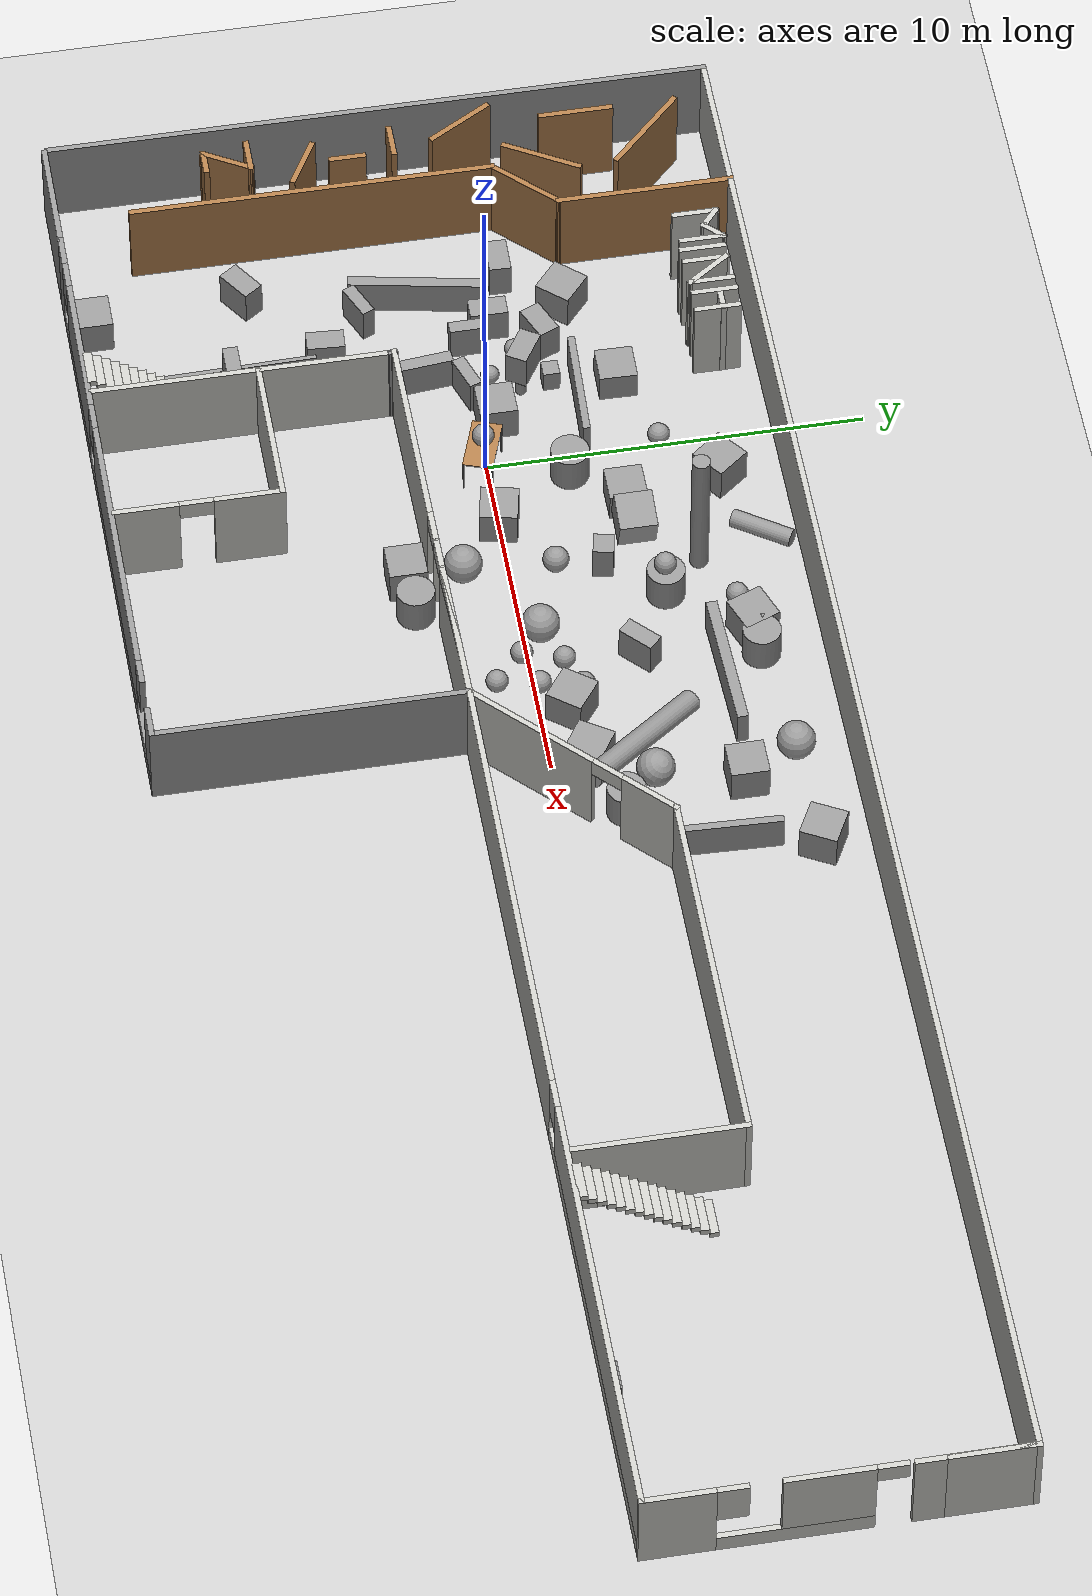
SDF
<sdf version="1.7">
 <world name="default">
  <light name="sun" type="directional">
   <pose>0 0 10 0 -0 0</pose>
   <diffuse>0.8 0.8 0.8 1</diffuse>
   <specular>0.2 0.2 0.2 1</specular>
   <attenuation>
    <range>1000</range>
    <constant>0.9</constant>
    <linear>0.01</linear>
    <quadratic>0.001</quadratic>
   </attenuation>
   <direction>-0.5 0.1 -0.9</direction>
   <spot><inner_angle>0</inner_angle><outer_angle>0</outer_angle><falloff>0</falloff></spot>
  </light>
  <model name="ground_plane">
   <static>1</static>
   <link name="link">
    <collision name="collision">
     <geometry><plane><normal>0 0 1</normal><size>100 100</size></plane></geometry>
     <surface>
      <contact><collide_bitmask>65535</collide_bitmask></contact>
      <friction><ode><mu>100</mu><mu2>50</mu2></ode></friction>
     </surface>
    </collision>
    <visual name="visual">
     <cast_shadows>0</cast_shadows>
     <geometry><plane><normal>0 0 1</normal><size>100 100</size></plane></geometry>
     <material>
      <script><uri>file://media/materials/scripts/gazebo.material</uri><name>Gazebo/Grey</name></script>
     </material>
    </visual>
   </link>
  </model>
  <gravity>0 0 -9.8</gravity>
  <magnetic_field>6e-06 2.3e-05 -4.2e-05</magnetic_field>
  <atmosphere type="adiabatic"/>
  <physics type="ode">
   <max_step_size>0.001</max_step_size>
   <real_time_factor>1</real_time_factor>
   <real_time_update_rate>1000</real_time_update_rate>
  </physics>
  <scene><ambient>0.4 0.4 0.4 1</ambient><background>0.7 0.7 0.7 1</background><shadows>1</shadows></scene>
  <spherical_coordinates>
   <surface_model>EARTH_WGS84</surface_model>
   <latitude_deg>0</latitude_deg>
   <longitude_deg>0</longitude_deg>
   <elevation>0</elevation>
   <heading_deg>0</heading_deg>
  </spherical_coordinates>
  <model name="buiding2">
   <pose>11.5475 -1.19599 0 0 -0 0</pose>
   <link name="Stairs_1">
    <visual name="Stairs_1_Visual_0">
     <pose>-14.5813 -5.44115 0.083333 0 -0 0</pose>
     <geometry><box><size>1 0.233333 0.166667</size></box></geometry>
     <material>
      <script><uri>file://media/materials/scripts/gazebo.material</uri><name>Gazebo/CeilingTiled</name></script>
      <ambient>1 1 1 1</ambient>
     </material>
     <meta><layer>0</layer></meta>
    </visual>
    <collision name="Stairs_1_Collision_0">
     <geometry><box><size>1 0.233333 0.166667</size></box></geometry>
     <pose>-14.5813 -5.44115 0.083333 0 -0 0</pose>
    </collision>
    <visual name="Stairs_1_Visual_1">
     <pose>-14.5813 -5.67448 0.25 0 -0 0</pose>
     <geometry><box><size>1 0.233333 0.166667</size></box></geometry>
     <material>
      <script><uri>file://media/materials/scripts/gazebo.material</uri><name>Gazebo/CeilingTiled</name></script>
      <ambient>1 1 1 1</ambient>
     </material>
     <meta><layer>0</layer></meta>
    </visual>
    <collision name="Stairs_1_Collision_1">
     <geometry><box><size>1 0.233333 0.166667</size></box></geometry>
     <pose>-14.5813 -5.67448 0.25 0 -0 0</pose>
    </collision>
    <visual name="Stairs_1_Visual_2">
     <pose>-14.5813 -5.90781 0.416667 0 -0 0</pose>
     <geometry><box><size>1 0.233333 0.166667</size></box></geometry>
     <material>
      <script><uri>file://media/materials/scripts/gazebo.material</uri><name>Gazebo/CeilingTiled</name></script>
      <ambient>1 1 1 1</ambient>
     </material>
     <meta><layer>0</layer></meta>
    </visual>
    <collision name="Stairs_1_Collision_2">
     <geometry><box><size>1 0.233333 0.166667</size></box></geometry>
     <pose>-14.5813 -5.90781 0.416667 0 -0 0</pose>
    </collision>
    <visual name="Stairs_1_Visual_3">
     <pose>-14.5813 -6.14115 0.583333 0 -0 0</pose>
     <geometry><box><size>1 0.233333 0.166667</size></box></geometry>
     <material>
      <script><uri>file://media/materials/scripts/gazebo.material</uri><name>Gazebo/CeilingTiled</name></script>
      <ambient>1 1 1 1</ambient>
     </material>
     <meta><layer>0</layer></meta>
    </visual>
    <collision name="Stairs_1_Collision_3">
     <geometry><box><size>1 0.233333 0.166667</size></box></geometry>
     <pose>-14.5813 -6.14115 0.583333 0 -0 0</pose>
    </collision>
    <visual name="Stairs_1_Visual_4">
     <pose>-14.5813 -6.37448 0.75 0 -0 0</pose>
     <geometry><box><size>1 0.233333 0.166667</size></box></geometry>
     <material>
      <script><uri>file://media/materials/scripts/gazebo.material</uri><name>Gazebo/CeilingTiled</name></script>
      <ambient>1 1 1 1</ambient>
     </material>
     <meta><layer>0</layer></meta>
    </visual>
    <collision name="Stairs_1_Collision_4">
     <geometry><box><size>1 0.233333 0.166667</size></box></geometry>
     <pose>-14.5813 -6.37448 0.75 0 -0 0</pose>
    </collision>
    <visual name="Stairs_1_Visual_5">
     <pose>-14.5813 -6.60781 0.916667 0 -0 0</pose>
     <geometry><box><size>1 0.233333 0.166667</size></box></geometry>
     <material>
      <script><uri>file://media/materials/scripts/gazebo.material</uri><name>Gazebo/CeilingTiled</name></script>
      <ambient>1 1 1 1</ambient>
     </material>
     <meta><layer>0</layer></meta>
    </visual>
    <collision name="Stairs_1_Collision_5">
     <geometry><box><size>1 0.233333 0.166667</size></box></geometry>
     <pose>-14.5813 -6.60781 0.916667 0 -0 0</pose>
    </collision>
    <visual name="Stairs_1_Visual_6">
     <pose>-14.5813 -6.84115 1.08333 0 -0 0</pose>
     <geometry><box><size>1 0.233333 0.166667</size></box></geometry>
     <material>
      <script><uri>file://media/materials/scripts/gazebo.material</uri><name>Gazebo/CeilingTiled</name></script>
      <ambient>1 1 1 1</ambient>
     </material>
     <meta><layer>0</layer></meta>
    </visual>
    <collision name="Stairs_1_Collision_6">
     <geometry><box><size>1 0.233333 0.166667</size></box></geometry>
     <pose>-14.5813 -6.84115 1.08333 0 -0 0</pose>
    </collision>
    <visual name="Stairs_1_Visual_7">
     <pose>-14.5813 -7.07448 1.25 0 -0 0</pose>
     <geometry><box><size>1 0.233333 0.166667</size></box></geometry>
     <material>
      <script><uri>file://media/materials/scripts/gazebo.material</uri><name>Gazebo/CeilingTiled</name></script>
      <ambient>1 1 1 1</ambient>
     </material>
     <meta><layer>0</layer></meta>
    </visual>
    <collision name="Stairs_1_Collision_7">
     <geometry><box><size>1 0.233333 0.166667</size></box></geometry>
     <pose>-14.5813 -7.07448 1.25 0 -0 0</pose>
    </collision>
    <visual name="Stairs_1_Visual_8">
     <pose>-14.5813 -7.30781 1.41667 0 -0 0</pose>
     <geometry><box><size>1 0.233333 0.166667</size></box></geometry>
     <material>
      <script><uri>file://media/materials/scripts/gazebo.material</uri><name>Gazebo/CeilingTiled</name></script>
      <ambient>1 1 1 1</ambient>
     </material>
     <meta><layer>0</layer></meta>
    </visual>
    <collision name="Stairs_1_Collision_8">
     <geometry><box><size>1 0.233333 0.166667</size></box></geometry>
     <pose>-14.5813 -7.30781 1.41667 0 -0 0</pose>
    </collision>
    <visual name="Stairs_1_Visual_9">
     <pose>-14.5813 -7.54115 1.58333 0 -0 0</pose>
     <geometry><box><size>1 0.233333 0.166667</size></box></geometry>
     <material>
      <script><uri>file://media/materials/scripts/gazebo.material</uri><name>Gazebo/CeilingTiled</name></script>
      <ambient>1 1 1 1</ambient>
     </material>
     <meta><layer>0</layer></meta>
    </visual>
    <collision name="Stairs_1_Collision_9">
     <geometry><box><size>1 0.233333 0.166667</size></box></geometry>
     <pose>-14.5813 -7.54115 1.58333 0 -0 0</pose>
    </collision>
    <visual name="Stairs_1_Visual_10">
     <pose>-14.5813 -7.77448 1.75 0 -0 0</pose>
     <geometry><box><size>1 0.233333 0.166667</size></box></geometry>
     <material>
      <script><uri>file://media/materials/scripts/gazebo.material</uri><name>Gazebo/CeilingTiled</name></script>
      <ambient>1 1 1 1</ambient>
     </material>
     <meta><layer>0</layer></meta>
    </visual>
    <collision name="Stairs_1_Collision_10">
     <geometry><box><size>1 0.233333 0.166667</size></box></geometry>
     <pose>-14.5813 -7.77448 1.75 0 -0 0</pose>
    </collision>
    <visual name="Stairs_1_Visual_11">
     <pose>-14.5813 -8.00781 1.91667 0 -0 0</pose>
     <geometry><box><size>1 0.233333 0.166667</size></box></geometry>
     <material>
      <script><uri>file://media/materials/scripts/gazebo.material</uri><name>Gazebo/CeilingTiled</name></script>
      <ambient>1 1 1 1</ambient>
     </material>
     <meta><layer>0</layer></meta>
    </visual>
    <collision name="Stairs_1_Collision_11">
     <geometry><box><size>1 0.233333 0.166667</size></box></geometry>
     <pose>-14.5813 -8.00781 1.91667 0 -0 0</pose>
    </collision>
    <visual name="Stairs_1_Visual_12">
     <pose>-14.5813 -8.24115 2.08333 0 -0 0</pose>
     <geometry><box><size>1 0.233333 0.166667</size></box></geometry>
     <material>
      <script><uri>file://media/materials/scripts/gazebo.material</uri><name>Gazebo/CeilingTiled</name></script>
      <ambient>1 1 1 1</ambient>
     </material>
     <meta><layer>0</layer></meta>
    </visual>
    <collision name="Stairs_1_Collision_12">
     <geometry><box><size>1 0.233333 0.166667</size></box></geometry>
     <pose>-14.5813 -8.24115 2.08333 0 -0 0</pose>
    </collision>
    <visual name="Stairs_1_Visual_13">
     <pose>-14.5813 -8.47448 2.25 0 -0 0</pose>
     <geometry><box><size>1 0.233333 0.166667</size></box></geometry>
     <material>
      <script><uri>file://media/materials/scripts/gazebo.material</uri><name>Gazebo/CeilingTiled</name></script>
      <ambient>1 1 1 1</ambient>
     </material>
     <meta><layer>0</layer></meta>
    </visual>
    <collision name="Stairs_1_Collision_13">
     <geometry><box><size>1 0.233333 0.166667</size></box></geometry>
     <pose>-14.5813 -8.47448 2.25 0 -0 0</pose>
    </collision>
    <visual name="Stairs_1_Visual_14">
     <pose>-14.5813 -8.70781 2.41667 0 -0 0</pose>
     <geometry><box><size>1 0.233333 0.166667</size></box></geometry>
     <material>
      <script><uri>file://media/materials/scripts/gazebo.material</uri><name>Gazebo/CeilingTiled</name></script>
      <ambient>1 1 1 1</ambient>
     </material>
     <meta><layer>0</layer></meta>
    </visual>
    <collision name="Stairs_1_Collision_14">
     <geometry><box><size>1 0.233333 0.166667</size></box></geometry>
     <pose>-14.5813 -8.70781 2.41667 0 -0 0</pose>
    </collision>
   </link>
   <link name="Stairs_4">
    <visual name="Stairs_4_Visual_0">
     <pose>12.8439 2.67013 0.083333 0 -0 0</pose>
     <geometry><box><size>1 0.233333 0.166667</size></box></geometry>
     <material>
      <script><uri>file://media/materials/scripts/gazebo.material</uri><name>Gazebo/CeilingTiled</name></script>
      <ambient>1 1 1 1</ambient>
     </material>
     <meta><layer>0</layer></meta>
    </visual>
    <collision name="Stairs_4_Collision_0">
     <geometry><box><size>1 0.233333 0.166667</size></box></geometry>
     <pose>12.8439 2.67013 0.083333 0 -0 0</pose>
    </collision>
    <visual name="Stairs_4_Visual_1">
     <pose>12.8439 2.4368 0.25 0 -0 0</pose>
     <geometry><box><size>1 0.233333 0.166667</size></box></geometry>
     <material>
      <script><uri>file://media/materials/scripts/gazebo.material</uri><name>Gazebo/CeilingTiled</name></script>
      <ambient>1 1 1 1</ambient>
     </material>
     <meta><layer>0</layer></meta>
    </visual>
    <collision name="Stairs_4_Collision_1">
     <geometry><box><size>1 0.233333 0.166667</size></box></geometry>
     <pose>12.8439 2.4368 0.25 0 -0 0</pose>
    </collision>
    <visual name="Stairs_4_Visual_2">
     <pose>12.8439 2.20347 0.416667 0 -0 0</pose>
     <geometry><box><size>1 0.233333 0.166667</size></box></geometry>
     <material>
      <script><uri>file://media/materials/scripts/gazebo.material</uri><name>Gazebo/CeilingTiled</name></script>
      <ambient>1 1 1 1</ambient>
     </material>
     <meta><layer>0</layer></meta>
    </visual>
    <collision name="Stairs_4_Collision_2">
     <geometry><box><size>1 0.233333 0.166667</size></box></geometry>
     <pose>12.8439 2.20347 0.416667 0 -0 0</pose>
    </collision>
    <visual name="Stairs_4_Visual_3">
     <pose>12.8439 1.97013 0.583333 0 -0 0</pose>
     <geometry><box><size>1 0.233333 0.166667</size></box></geometry>
     <material>
      <script><uri>file://media/materials/scripts/gazebo.material</uri><name>Gazebo/CeilingTiled</name></script>
      <ambient>1 1 1 1</ambient>
     </material>
     <meta><layer>0</layer></meta>
    </visual>
    <collision name="Stairs_4_Collision_3">
     <geometry><box><size>1 0.233333 0.166667</size></box></geometry>
     <pose>12.8439 1.97013 0.583333 0 -0 0</pose>
    </collision>
    <visual name="Stairs_4_Visual_4">
     <pose>12.8439 1.7368 0.75 0 -0 0</pose>
     <geometry><box><size>1 0.233333 0.166667</size></box></geometry>
     <material>
      <script><uri>file://media/materials/scripts/gazebo.material</uri><name>Gazebo/CeilingTiled</name></script>
      <ambient>1 1 1 1</ambient>
     </material>
     <meta><layer>0</layer></meta>
    </visual>
    <collision name="Stairs_4_Collision_4">
     <geometry><box><size>1 0.233333 0.166667</size></box></geometry>
     <pose>12.8439 1.7368 0.75 0 -0 0</pose>
    </collision>
    <visual name="Stairs_4_Visual_5">
     <pose>12.8439 1.50346 0.916667 0 -0 0</pose>
     <geometry><box><size>1 0.233333 0.166667</size></box></geometry>
     <material>
      <script><uri>file://media/materials/scripts/gazebo.material</uri><name>Gazebo/CeilingTiled</name></script>
      <ambient>1 1 1 1</ambient>
     </material>
     <meta><layer>0</layer></meta>
    </visual>
    <collision name="Stairs_4_Collision_5">
     <geometry><box><size>1 0.233333 0.166667</size></box></geometry>
     <pose>12.8439 1.50346 0.916667 0 -0 0</pose>
    </collision>
    <visual name="Stairs_4_Visual_6">
     <pose>12.8439 1.27013 1.08333 0 -0 0</pose>
     <geometry><box><size>1 0.233333 0.166667</size></box></geometry>
     <material>
      <script><uri>file://media/materials/scripts/gazebo.material</uri><name>Gazebo/CeilingTiled</name></script>
      <ambient>1 1 1 1</ambient>
     </material>
     <meta><layer>0</layer></meta>
    </visual>
    <collision name="Stairs_4_Collision_6">
     <geometry><box><size>1 0.233333 0.166667</size></box></geometry>
     <pose>12.8439 1.27013 1.08333 0 -0 0</pose>
    </collision>
    <visual name="Stairs_4_Visual_7">
     <pose>12.8439 1.0368 1.25 0 -0 0</pose>
     <geometry><box><size>1 0.233333 0.166667</size></box></geometry>
     <material>
      <script><uri>file://media/materials/scripts/gazebo.material</uri><name>Gazebo/CeilingTiled</name></script>
      <ambient>1 1 1 1</ambient>
     </material>
     <meta><layer>0</layer></meta>
    </visual>
    <collision name="Stairs_4_Collision_7">
     <geometry><box><size>1 0.233333 0.166667</size></box></geometry>
     <pose>12.8439 1.0368 1.25 0 -0 0</pose>
    </collision>
    <visual name="Stairs_4_Visual_8">
     <pose>12.8439 0.803464 1.41667 0 -0 0</pose>
     <geometry><box><size>1 0.233333 0.166667</size></box></geometry>
     <material>
      <script><uri>file://media/materials/scripts/gazebo.material</uri><name>Gazebo/CeilingTiled</name></script>
      <ambient>1 1 1 1</ambient>
     </material>
     <meta><layer>0</layer></meta>
    </visual>
    <collision name="Stairs_4_Collision_8">
     <geometry><box><size>1 0.233333 0.166667</size></box></geometry>
     <pose>12.8439 0.803464 1.41667 0 -0 0</pose>
    </collision>
    <visual name="Stairs_4_Visual_9">
     <pose>12.8439 0.570131 1.58333 0 -0 0</pose>
     <geometry><box><size>1 0.233333 0.166667</size></box></geometry>
     <material>
      <script><uri>file://media/materials/scripts/gazebo.material</uri><name>Gazebo/CeilingTiled</name></script>
      <ambient>1 1 1 1</ambient>
     </material>
     <meta><layer>0</layer></meta>
    </visual>
    <collision name="Stairs_4_Collision_9">
     <geometry><box><size>1 0.233333 0.166667</size></box></geometry>
     <pose>12.8439 0.570131 1.58333 0 -0 0</pose>
    </collision>
    <visual name="Stairs_4_Visual_10">
     <pose>12.8439 0.336798 1.75 0 -0 0</pose>
     <geometry><box><size>1 0.233333 0.166667</size></box></geometry>
     <material>
      <script><uri>file://media/materials/scripts/gazebo.material</uri><name>Gazebo/CeilingTiled</name></script>
      <ambient>1 1 1 1</ambient>
     </material>
     <meta><layer>0</layer></meta>
    </visual>
    <collision name="Stairs_4_Collision_10">
     <geometry><box><size>1 0.233333 0.166667</size></box></geometry>
     <pose>12.8439 0.336798 1.75 0 -0 0</pose>
    </collision>
    <visual name="Stairs_4_Visual_11">
     <pose>12.8439 0.103464 1.91667 0 -0 0</pose>
     <geometry><box><size>1 0.233333 0.166667</size></box></geometry>
     <material>
      <script><uri>file://media/materials/scripts/gazebo.material</uri><name>Gazebo/CeilingTiled</name></script>
      <ambient>1 1 1 1</ambient>
     </material>
     <meta><layer>0</layer></meta>
    </visual>
    <collision name="Stairs_4_Collision_11">
     <geometry><box><size>1 0.233333 0.166667</size></box></geometry>
     <pose>12.8439 0.103464 1.91667 0 -0 0</pose>
    </collision>
    <visual name="Stairs_4_Visual_12">
     <pose>12.8439 -0.129869 2.08333 0 -0 0</pose>
     <geometry><box><size>1 0.233333 0.166667</size></box></geometry>
     <material>
      <script><uri>file://media/materials/scripts/gazebo.material</uri><name>Gazebo/CeilingTiled</name></script>
      <ambient>1 1 1 1</ambient>
     </material>
     <meta><layer>0</layer></meta>
    </visual>
    <collision name="Stairs_4_Collision_12">
     <geometry><box><size>1 0.233333 0.166667</size></box></geometry>
     <pose>12.8439 -0.129869 2.08333 0 -0 0</pose>
    </collision>
    <visual name="Stairs_4_Visual_13">
     <pose>12.8439 -0.363202 2.25 0 -0 0</pose>
     <geometry><box><size>1 0.233333 0.166667</size></box></geometry>
     <material>
      <script><uri>file://media/materials/scripts/gazebo.material</uri><name>Gazebo/CeilingTiled</name></script>
      <ambient>1 1 1 1</ambient>
     </material>
     <meta><layer>0</layer></meta>
    </visual>
    <collision name="Stairs_4_Collision_13">
     <geometry><box><size>1 0.233333 0.166667</size></box></geometry>
     <pose>12.8439 -0.363202 2.25 0 -0 0</pose>
    </collision>
    <visual name="Stairs_4_Visual_14">
     <pose>12.8439 -0.596536 2.41667 0 -0 0</pose>
     <geometry><box><size>1 0.233333 0.166667</size></box></geometry>
     <material>
      <script><uri>file://media/materials/scripts/gazebo.material</uri><name>Gazebo/CeilingTiled</name></script>
      <ambient>1 1 1 1</ambient>
     </material>
     <meta><layer>0</layer></meta>
    </visual>
    <collision name="Stairs_4_Collision_14">
     <geometry><box><size>1 0.233333 0.166667</size></box></geometry>
     <pose>12.8439 -0.596536 2.41667 0 -0 0</pose>
    </collision>
   </link>
   <link name="Wall_101">
    <collision name="Wall_101_Collision">
     <geometry><box><size>1.43908 0.15 2.5</size></box></geometry>
     <pose>0 0 1.25 0 -0 0</pose>
    </collision>
    <visual name="Wall_101_Visual">
     <pose>0 0 1.25 0 -0 0</pose>
     <geometry><box><size>1.43908 0.15 2.5</size></box></geometry>
     <material>
      <script><uri>file://media/materials/scripts/gazebo.material</uri><name>Gazebo/CeilingTiled</name></script>
      <ambient>1 1 1 1</ambient>
     </material>
     <meta><layer>0</layer></meta>
    </visual>
    <pose>-15.1891 7.7092 0 0 -0 -0.97117</pose>
   </link>
   <link name="Wall_102">
    <collision name="Wall_102_Collision">
     <geometry><box><size>1.25 0.15 2.5</size></box></geometry>
     <pose>0 0 1.25 0 -0 0</pose>
    </collision>
    <visual name="Wall_102_Visual">
     <pose>0 0 1.25 0 -0 0</pose>
     <geometry><box><size>1.25 0.15 2.5</size></box></geometry>
     <material>
      <script><uri>file://media/materials/scripts/gazebo.material</uri><name>Gazebo/CeilingTiled</name></script>
      <ambient>1 1 1 1</ambient>
     </material>
     <meta><layer>0</layer></meta>
    </visual>
    <pose>-14.8254 7.7271 0 0 -0 1.5708</pose>
   </link>
   <link name="Wall_104">
    <collision name="Wall_104_Collision">
     <geometry><box><size>1.25 0.15 2.5</size></box></geometry>
     <pose>0 0 1.25 0 -0 0</pose>
    </collision>
    <visual name="Wall_104_Visual">
     <pose>0 0 1.25 0 -0 0</pose>
     <geometry><box><size>1.25 0.15 2.5</size></box></geometry>
     <material>
      <script><uri>file://media/materials/scripts/gazebo.material</uri><name>Gazebo/CeilingTiled</name></script>
      <ambient>1 1 1 1</ambient>
     </material>
     <meta><layer>0</layer></meta>
    </visual>
    <pose>-14.4603 7.7395 0 0 -0 -1.5708</pose>
   </link>
   <link name="Wall_106">
    <collision name="Wall_106_Collision">
     <geometry><box><size>1.25 0.15 2.5</size></box></geometry>
     <pose>0 0 1.25 0 -0 0</pose>
    </collision>
    <visual name="Wall_106_Visual">
     <pose>0 0 1.25 0 -0 0</pose>
     <geometry><box><size>1.25 0.15 2.5</size></box></geometry>
     <material>
      <script><uri>file://media/materials/scripts/gazebo.material</uri><name>Gazebo/CeilingTiled</name></script>
      <ambient>1 1 1 1</ambient>
     </material>
     <meta><layer>0</layer></meta>
    </visual>
    <pose>-13.878 7.71348 0 0 -0 -1.5708</pose>
   </link>
   <link name="Wall_108">
    <collision name="Wall_108_Collision">
     <geometry><box><size>0.75 0.15 2.5</size></box></geometry>
     <pose>0 0 1.25 0 -0 0</pose>
    </collision>
    <visual name="Wall_108_Visual">
     <pose>0 0 1.25 0 -0 0</pose>
     <geometry><box><size>0.75 0.15 2.5</size></box></geometry>
     <material>
      <script><uri>file://media/materials/scripts/gazebo.material</uri><name>Gazebo/CeilingTiled</name></script>
      <ambient>1 1 1 1</ambient>
     </material>
     <meta><layer>0</layer></meta>
    </visual>
    <pose>-14.1689 7.87014 0 0 -0 0</pose>
   </link>
   <link name="Wall_25">
    <pose>-10.725 -8.85281 0 0 -0 0</pose>
    <visual name="Wall_25_Visual_0">
     <pose>-7.92935 0 1.25 0 -0 0</pose>
     <geometry><box><size>0.891293 0.15 2.5</size></box></geometry>
     <material>
      <script><uri>file://media/materials/scripts/gazebo.material</uri><name>Gazebo/Grey</name></script>
      <ambient>1 1 1 1</ambient>
     </material>
     <meta><layer>0</layer></meta>
    </visual>
    <collision name="Wall_25_Collision_0">
     <geometry><box><size>0.891293 0.15 2.5</size></box></geometry>
     <pose>-7.92935 0 1.25 0 -0 0</pose>
    </collision>
    <visual name="Wall_25_Visual_1">
     <pose>0.445646 0 0.25 0 -0 0</pose>
     <geometry><box><size>15.8587 0.15 0.5</size></box></geometry>
     <material>
      <script><uri>file://media/materials/scripts/gazebo.material</uri><name>Gazebo/Grey</name></script>
      <ambient>1 1 1 1</ambient>
     </material>
     <meta><layer>0</layer></meta>
    </visual>
    <collision name="Wall_25_Collision_1">
     <geometry><box><size>15.8587 0.15 0.5</size></box></geometry>
     <pose>0.445646 0 0.25 0 -0 0</pose>
    </collision>
    <visual name="Wall_25_Visual_2">
     <pose>-4.64452 0 1.5 0 -0 0</pose>
     <geometry><box><size>4.07838 0.15 2</size></box></geometry>
     <material>
      <script><uri>file://media/materials/scripts/gazebo.material</uri><name>Gazebo/Grey</name></script>
      <ambient>1 1 1 1</ambient>
     </material>
     <meta><layer>0</layer></meta>
    </visual>
    <collision name="Wall_25_Collision_2">
     <geometry><box><size>4.07838 0.15 2</size></box></geometry>
     <pose>-4.64452 0 1.5 0 -0 0</pose>
    </collision>
    <visual name="Wall_25_Visual_3">
     <pose>2.06577 0 1.5 0 -0 0</pose>
     <geometry><box><size>7.74221 0.15 2</size></box></geometry>
     <material>
      <script><uri>file://media/materials/scripts/gazebo.material</uri><name>Gazebo/Grey</name></script>
      <ambient>1 1 1 1</ambient>
     </material>
     <meta><layer>0</layer></meta>
    </visual>
    <collision name="Wall_25_Collision_3">
     <geometry><box><size>7.74221 0.15 2</size></box></geometry>
     <pose>2.06577 0 1.5 0 -0 0</pose>
    </collision>
    <visual name="Wall_25_Visual_4">
     <pose>7.91345 0 1.5 0 -0 0</pose>
     <geometry><box><size>0.9231 0.15 2</size></box></geometry>
     <material>
      <script><uri>file://media/materials/scripts/gazebo.material</uri><name>Gazebo/Grey</name></script>
      <ambient>1 1 1 1</ambient>
     </material>
     <meta><layer>0</layer></meta>
    </visual>
    <collision name="Wall_25_Collision_4">
     <geometry><box><size>0.9231 0.15 2</size></box></geometry>
     <pose>7.91345 0 1.5 0 -0 0</pose>
    </collision>
    <visual name="Wall_25_Visual_5">
     <pose>-7.08371 0 1.9 0 -0 0</pose>
     <geometry><box><size>0.8 0.15 1.2</size></box></geometry>
     <material>
      <script><uri>file://media/materials/scripts/gazebo.material</uri><name>Gazebo/Grey</name></script>
      <ambient>1 1 1 1</ambient>
     </material>
     <meta><layer>0</layer></meta>
    </visual>
    <collision name="Wall_25_Collision_5">
     <geometry><box><size>0.8 0.15 1.2</size></box></geometry>
     <pose>-7.08371 0 1.9 0 -0 0</pose>
    </collision>
    <visual name="Wall_25_Visual_6">
     <pose>-2.20533 0 1.9 0 -0 0</pose>
     <geometry><box><size>0.8 0.15 1.2</size></box></geometry>
     <material>
      <script><uri>file://media/materials/scripts/gazebo.material</uri><name>Gazebo/Grey</name></script>
      <ambient>1 1 1 1</ambient>
     </material>
     <meta><layer>0</layer></meta>
    </visual>
    <collision name="Wall_25_Collision_6">
     <geometry><box><size>0.8 0.15 1.2</size></box></geometry>
     <pose>-2.20533 0 1.9 0 -0 0</pose>
    </collision>
    <visual name="Wall_25_Visual_7">
     <pose>6.29439 0 1.9 0 -0 0</pose>
     <geometry><box><size>0.715025 0.15 1.2</size></box></geometry>
     <material>
      <script><uri>file://media/materials/scripts/gazebo.material</uri><name>Gazebo/Grey</name></script>
      <ambient>1 1 1 1</ambient>
     </material>
     <meta><layer>0</layer></meta>
    </visual>
    <collision name="Wall_25_Collision_7">
     <geometry><box><size>0.715025 0.15 1.2</size></box></geometry>
     <pose>6.29439 0 1.9 0 -0 0</pose>
    </collision>
   </link>
   <link name="Wall_26">
    <collision name="Wall_26_Collision">
     <geometry><box><size>8.25 0.15 2.5</size></box></geometry>
     <pose>0 0 1.25 0 -0 0</pose>
    </collision>
    <visual name="Wall_26_Visual">
     <pose>0 0 1.25 0 -0 0</pose>
     <geometry><box><size>8.25 0.15 2.5</size></box></geometry>
     <material>
      <script><uri>file://media/materials/scripts/gazebo.material</uri><name>Gazebo/Grey</name></script>
      <ambient>1 1 1 1</ambient>
     </material>
     <meta><layer>0</layer></meta>
    </visual>
    <pose>-2.425 -4.80281 0 0 -0 1.5708</pose>
   </link>
   <link name="Wall_27">
    <pose>9.875 -0.752815 0 0 -0 0</pose>
    <visual name="Wall_27_Visual_0">
     <pose>-6.22342 0 1.25 0 -0 0</pose>
     <geometry><box><size>12.3032 0.15 2.5</size></box></geometry>
     <material>
      <script><uri>file://media/materials/scripts/gazebo.material</uri><name>Gazebo/CeilingTiled</name></script>
      <ambient>1 1 1 1</ambient>
     </material>
     <meta><layer>0</layer></meta>
    </visual>
    <collision name="Wall_27_Collision_0">
     <geometry><box><size>12.3032 0.15 2.5</size></box></geometry>
     <pose>-6.22342 0 1.25 0 -0 0</pose>
    </collision>
    <visual name="Wall_27_Visual_1">
     <pose>6.15158 0 0.25 0 -0 0</pose>
     <geometry><box><size>12.4468 0.15 0.5</size></box></geometry>
     <material>
      <script><uri>file://media/materials/scripts/gazebo.material</uri><name>Gazebo/CeilingTiled</name></script>
      <ambient>1 1 1 1</ambient>
     </material>
     <meta><layer>0</layer></meta>
    </visual>
    <collision name="Wall_27_Collision_1">
     <geometry><box><size>12.4468 0.15 0.5</size></box></geometry>
     <pose>6.15158 0 0.25 0 -0 0</pose>
    </collision>
    <visual name="Wall_27_Visual_2">
     <pose>6.55158 0 1.5 0 -0 0</pose>
     <geometry><box><size>11.6468 0.15 2</size></box></geometry>
     <material>
      <script><uri>file://media/materials/scripts/gazebo.material</uri><name>Gazebo/CeilingTiled</name></script>
      <ambient>1 1 1 1</ambient>
     </material>
     <meta><layer>0</layer></meta>
    </visual>
    <collision name="Wall_27_Collision_2">
     <geometry><box><size>11.6468 0.15 2</size></box></geometry>
     <pose>6.55158 0 1.5 0 -0 0</pose>
    </collision>
    <visual name="Wall_27_Visual_3">
     <pose>0.328163 0 1.9 0 -0 0</pose>
     <geometry><box><size>0.8 0.15 1.2</size></box></geometry>
     <material>
      <script><uri>file://media/materials/scripts/gazebo.material</uri><name>Gazebo/CeilingTiled</name></script>
      <ambient>1 1 1 1</ambient>
     </material>
     <meta><layer>0</layer></meta>
    </visual>
    <collision name="Wall_27_Collision_3">
     <geometry><box><size>0.8 0.15 1.2</size></box></geometry>
     <pose>0.328163 0 1.9 0 -0 0</pose>
    </collision>
   </link>
   <link name="Wall_28">
    <pose>22.175 4.04718 0 0 -0 1.5708</pose>
    <visual name="Wall_28_Visual_0">
     <pose>-3.92954 0 1.25 0 -0 0</pose>
     <geometry><box><size>1.89092 0.15 2.5</size></box></geometry>
     <material>
      <script><uri>file://media/materials/scripts/gazebo.material</uri><name>Gazebo/CeilingTiled</name></script>
      <ambient>1 1 1 1</ambient>
     </material>
     <meta><layer>0</layer></meta>
    </visual>
    <collision name="Wall_28_Collision_0">
     <geometry><box><size>1.89092 0.15 2.5</size></box></geometry>
     <pose>-3.92954 0 1.25 0 -0 0</pose>
    </collision>
    <visual name="Wall_28_Visual_1">
     <pose>3.32447 0 1.25 0 -0 0</pose>
     <geometry><box><size>3.10107 0.15 2.5</size></box></geometry>
     <material>
      <script><uri>file://media/materials/scripts/gazebo.material</uri><name>Gazebo/CeilingTiled</name></script>
      <ambient>1 1 1 1</ambient>
     </material>
     <meta><layer>0</layer></meta>
    </visual>
    <collision name="Wall_28_Collision_1">
     <geometry><box><size>3.10107 0.15 2.5</size></box></geometry>
     <pose>3.32447 0 1.25 0 -0 0</pose>
    </collision>
    <visual name="Wall_28_Visual_2">
     <pose>3.71992 0 1.25 0 -0 0</pose>
     <geometry><box><size>2.31016 0.15 2.5</size></box></geometry>
     <material>
      <script><uri>file://media/materials/scripts/gazebo.material</uri><name>Gazebo/CeilingTiled</name></script>
      <ambient>1 1 1 1</ambient>
     </material>
     <meta><layer>0</layer></meta>
    </visual>
    <collision name="Wall_28_Collision_2">
     <geometry><box><size>2.31016 0.15 2.5</size></box></geometry>
     <pose>3.71992 0 1.25 0 -0 0</pose>
    </collision>
    <visual name="Wall_28_Visual_3">
     <pose>-1.05507 0 0.25 0 -0 0</pose>
     <geometry><box><size>3.85801 0.15 0.5</size></box></geometry>
     <material>
      <script><uri>file://media/materials/scripts/gazebo.material</uri><name>Gazebo/CeilingTiled</name></script>
      <ambient>1 1 1 1</ambient>
     </material>
     <meta><layer>0</layer></meta>
    </visual>
    <collision name="Wall_28_Collision_3">
     <geometry><box><size>3.85801 0.15 0.5</size></box></geometry>
     <pose>-1.05507 0 0.25 0 -0 0</pose>
    </collision>
    <visual name="Wall_28_Visual_4">
     <pose>-0.260708 0 1.5 0 -0 0</pose>
     <geometry><box><size>2.26928 0.15 2</size></box></geometry>
     <material>
      <script><uri>file://media/materials/scripts/gazebo.material</uri><name>Gazebo/CeilingTiled</name></script>
      <ambient>1 1 1 1</ambient>
     </material>
     <meta><layer>0</layer></meta>
    </visual>
    <collision name="Wall_28_Collision_4">
     <geometry><box><size>2.26928 0.15 2</size></box></geometry>
     <pose>-0.260708 0 1.5 0 -0 0</pose>
    </collision>
    <visual name="Wall_28_Visual_5">
     <pose>-2.58971 0 1.9 0 -0 0</pose>
     <geometry><box><size>0.788728 0.15 1.2</size></box></geometry>
     <material>
      <script><uri>file://media/materials/scripts/gazebo.material</uri><name>Gazebo/CeilingTiled</name></script>
      <ambient>1 1 1 1</ambient>
     </material>
     <meta><layer>0</layer></meta>
    </visual>
    <collision name="Wall_28_Collision_5">
     <geometry><box><size>0.788728 0.15 1.2</size></box></geometry>
     <pose>-2.58971 0 1.9 0 -0 0</pose>
    </collision>
    <visual name="Wall_28_Visual_6">
     <pose>1.26939 0 2.25 0 -0 0</pose>
     <geometry><box><size>0.790907 0.15 0.5</size></box></geometry>
     <material>
      <script><uri>file://media/materials/scripts/gazebo.material</uri><name>Gazebo/CeilingTiled</name></script>
      <ambient>1 1 1 1</ambient>
     </material>
     <meta><layer>0</layer></meta>
    </visual>
    <collision name="Wall_28_Collision_6">
     <geometry><box><size>0.790907 0.15 0.5</size></box></geometry>
     <pose>1.26939 0 2.25 0 -0 0</pose>
    </collision>
   </link>
   <link name="Wall_29">
    <collision name="Wall_29_Collision">
     <geometry><box><size>44.5 0.15 2.5</size></box></geometry>
     <pose>0 0 1.25 0 -0 0</pose>
    </collision>
    <visual name="Wall_29_Visual">
     <pose>0 0 1.25 0 -0 0</pose>
     <geometry><box><size>44.5 0.15 2.5</size></box></geometry>
     <material>
      <script><uri>file://media/materials/scripts/gazebo.material</uri><name>Gazebo/CeilingTiled</name></script>
      <ambient>1 1 1 1</ambient>
     </material>
     <meta><layer>0</layer></meta>
    </visual>
    <pose>0 8.84718 0 0 -0 3.14159</pose>
   </link>
   <link name="Wall_30">
    <collision name="Wall_30_Collision">
     <geometry><box><size>17.75 0.15 2.5</size></box></geometry>
     <pose>0 0 1.25 0 -0 0</pose>
    </collision>
    <visual name="Wall_30_Visual">
     <pose>0 0 1.25 0 -0 0</pose>
     <geometry><box><size>17.75 0.15 2.5</size></box></geometry>
     <material>
      <script><uri>file://media/materials/scripts/gazebo.material</uri><name>Gazebo/Grey</name></script>
      <ambient>1 1 1 1</ambient>
     </material>
     <meta><layer>0</layer></meta>
    </visual>
    <pose>-22.175 0.047185 0 0 -0 -1.5708</pose>
   </link>
   <link name="Wall_33">
    <collision name="Wall_33_Collision">
     <geometry><box><size>3.25 0.15 2.5</size></box></geometry>
     <pose>0 0 1.25 0 -0 0</pose>
    </collision>
    <visual name="Wall_33_Visual">
     <pose>0 0 1.25 0 -0 0</pose>
     <geometry><box><size>3.25 0.15 2.5</size></box></geometry>
     <material>
      <script><uri>file://media/materials/scripts/gazebo.material</uri><name>Gazebo/Grey</name></script>
      <ambient>1 1 1 1</ambient>
     </material>
     <meta><layer>0</layer></meta>
    </visual>
    <pose>-20.575 -8.85281 0 0 -0 3.14159</pose>
   </link>
   <link name="Wall_35">
    <collision name="Wall_35_Collision">
     <geometry><box><size>8 0.15 2.5</size></box></geometry>
     <pose>0 0 1.25 0 -0 0</pose>
    </collision>
    <visual name="Wall_35_Visual">
     <pose>0 0 1.25 0 -0 0</pose>
     <geometry><box><size>8 0.15 2.5</size></box></geometry>
     <material>
      <script><uri>file://media/materials/scripts/gazebo.material</uri><name>Gazebo/CeilingTiled</name></script>
      <ambient>1 1 1 1</ambient>
     </material>
     <meta><layer>0</layer></meta>
    </visual>
    <pose>-13.7705 -4.85682 0 0 -0 1.5708</pose>
   </link>
   <link name="Wall_36">
    <collision name="Wall_36_Collision">
     <geometry><box><size>0.15 0.15 2.5</size></box></geometry>
     <pose>0 0 1.25 0 -0 0</pose>
    </collision>
    <visual name="Wall_36_Visual">
     <pose>0 0 1.25 0 -0 0</pose>
     <geometry><box><size>0.15 0.15 2.5</size></box></geometry>
     <material>
      <script><uri>file://media/materials/scripts/gazebo.material</uri><name>Gazebo/Grey</name></script>
      <ambient>1 1 1 1</ambient>
     </material>
     <meta><layer>0</layer></meta>
    </visual>
    <pose>-13.7705 -0.931816 0 0 -0 0</pose>
   </link>
   <link name="Wall_37">
    <collision name="Wall_37_Collision">
     <geometry><box><size>0.25 0.15 2.5</size></box></geometry>
     <pose>0 0 1.25 0 -0 0</pose>
    </collision>
    <visual name="Wall_37_Visual">
     <pose>0 0 1.25 0 -0 0</pose>
     <geometry><box><size>0.25 0.15 2.5</size></box></geometry>
     <material>
      <script><uri>file://media/materials/scripts/gazebo.material</uri><name>Gazebo/Grey</name></script>
      <ambient>1 1 1 1</ambient>
     </material>
     <meta><layer>0</layer></meta>
    </visual>
    <pose>-13.7835 -0.88352 0 0 -0 1.8326</pose>
   </link>
   <link name="Wall_38">
    <pose>-8.1107 -0.794019 0 0 -0 0.007247</pose>
    <visual name="Wall_38_Visual_0">
     <pose>-2.98878 0 1.25 0 -0 0</pose>
     <geometry><box><size>5.54414 0.15 2.5</size></box></geometry>
     <material>
      <script><uri>file://media/materials/scripts/gazebo.material</uri><name>Gazebo/CeilingTiled</name></script>
      <ambient>1 1 1 1</ambient>
     </material>
     <meta><layer>0</layer></meta>
    </visual>
    <collision name="Wall_38_Collision_0">
     <geometry><box><size>5.54414 0.15 2.5</size></box></geometry>
     <pose>-2.98878 0 1.25 0 -0 0</pose>
    </collision>
    <visual name="Wall_38_Visual_1">
     <pose>0.703957 0 1.25 0 -0 0</pose>
     <geometry><box><size>0.041335 0.15 2.5</size></box></geometry>
     <material>
      <script><uri>file://media/materials/scripts/gazebo.material</uri><name>Gazebo/CeilingTiled</name></script>
      <ambient>1 1 1 1</ambient>
     </material>
     <meta><layer>0</layer></meta>
    </visual>
    <collision name="Wall_38_Collision_1">
     <geometry><box><size>0.041335 0.15 2.5</size></box></geometry>
     <pose>0.703957 0 1.25 0 -0 0</pose>
    </collision>
    <visual name="Wall_38_Visual_2">
     <pose>3.66981 0 1.25 0 -0 0</pose>
     <geometry><box><size>4.18208 0.15 2.5</size></box></geometry>
     <material>
      <script><uri>file://media/materials/scripts/gazebo.material</uri><name>Gazebo/CeilingTiled</name></script>
      <ambient>1 1 1 1</ambient>
     </material>
     <meta><layer>0</layer></meta>
    </visual>
    <collision name="Wall_38_Collision_2">
     <geometry><box><size>4.18208 0.15 2.5</size></box></geometry>
     <pose>3.66981 0 1.25 0 -0 0</pose>
    </collision>
    <visual name="Wall_38_Visual_3">
     <pose>3.69274 0 1.25 0 -0 0</pose>
     <geometry><box><size>4.13623 0.15 2.5</size></box></geometry>
     <material>
      <script><uri>file://media/materials/scripts/gazebo.material</uri><name>Gazebo/CeilingTiled</name></script>
      <ambient>1 1 1 1</ambient>
     </material>
     <meta><layer>0</layer></meta>
    </visual>
    <collision name="Wall_38_Collision_3">
     <geometry><box><size>4.13623 0.15 2.5</size></box></geometry>
     <pose>3.69274 0 1.25 0 -0 0</pose>
    </collision>
    <visual name="Wall_38_Visual_4">
     <pose>0.231032 0 2.25 0 -0 0</pose>
     <geometry><box><size>0.895486 0.15 0.5</size></box></geometry>
     <material>
      <script><uri>file://media/materials/scripts/gazebo.material</uri><name>Gazebo/CeilingTiled</name></script>
      <ambient>1 1 1 1</ambient>
     </material>
     <meta><layer>0</layer></meta>
    </visual>
    <collision name="Wall_38_Collision_4">
     <geometry><box><size>0.895486 0.15 0.5</size></box></geometry>
     <pose>0.231032 0 2.25 0 -0 0</pose>
    </collision>
    <visual name="Wall_38_Visual_5">
     <pose>1.1517 0 2.25 0 -0 0</pose>
     <geometry><box><size>0.854152 0.15 0.5</size></box></geometry>
     <material>
      <script><uri>file://media/materials/scripts/gazebo.material</uri><name>Gazebo/CeilingTiled</name></script>
      <ambient>1 1 1 1</ambient>
     </material>
     <meta><layer>0</layer></meta>
    </visual>
    <collision name="Wall_38_Collision_5">
     <geometry><box><size>0.854152 0.15 0.5</size></box></geometry>
     <pose>1.1517 0 2.25 0 -0 0</pose>
    </collision>
   </link>
   <link name="Wall_40">
    <collision name="Wall_40_Collision">
     <geometry><box><size>2.75 0.15 2.5</size></box></geometry>
     <pose>0 0 1.25 0 -0 0</pose>
    </collision>
    <visual name="Wall_40_Visual">
     <pose>0 0 1.25 0 -0 0</pose>
     <geometry><box><size>2.75 0.15 2.5</size></box></geometry>
     <material>
      <script><uri>file://media/materials/scripts/gazebo.material</uri><name>Gazebo/Wood</name></script>
      <ambient>1 1 1 1</ambient>
     </material>
     <meta><layer>0</layer></meta>
    </visual>
    <pose>-20.2769 6.95185 0 0 -0 -0.785398</pose>
   </link>
   <link name="Wall_42">
    <collision name="Wall_42_Collision">
     <geometry><box><size>2 0.15 2.5</size></box></geometry>
     <pose>0 0 1.25 0 -0 0</pose>
    </collision>
    <visual name="Wall_42_Visual">
     <pose>0 0 1.25 0 -0 0</pose>
     <geometry><box><size>2 0.15 2.5</size></box></geometry>
     <material>
      <script><uri>file://media/materials/scripts/gazebo.material</uri><name>Gazebo/Wood</name></script>
      <ambient>1 1 1 1</ambient>
     </material>
     <meta><layer>0</layer></meta>
    </visual>
    <pose>-21.1962 5.22471 0 0 -0 -1.5708</pose>
   </link>
   <link name="Wall_44">
    <collision name="Wall_44_Collision">
     <geometry><box><size>2.25 0.15 2.5</size></box></geometry>
     <pose>0 0 1.25 0 -0 0</pose>
    </collision>
    <visual name="Wall_44_Visual">
     <pose>0 0 1.25 0 -0 0</pose>
     <geometry><box><size>2.25 0.15 2.5</size></box></geometry>
     <material>
      <script><uri>file://media/materials/scripts/gazebo.material</uri><name>Gazebo/Wood</name></script>
      <ambient>1 1 1 1</ambient>
     </material>
     <meta><layer>0</layer></meta>
    </visual>
    <pose>-19.8137 4.07728 0 0 -0 -2.0944</pose>
   </link>
   <link name="Wall_46">
    <collision name="Wall_46_Collision">
     <geometry><box><size>2 0.15 2.5</size></box></geometry>
     <pose>0 0 1.25 0 -0 0</pose>
    </collision>
    <visual name="Wall_46_Visual">
     <pose>0 0 1.25 0 -0 0</pose>
     <geometry><box><size>2 0.15 2.5</size></box></geometry>
     <material>
      <script><uri>file://media/materials/scripts/gazebo.material</uri><name>Gazebo/Wood</name></script>
      <ambient>1 1 1 1</ambient>
     </material>
     <meta><layer>0</layer></meta>
    </visual>
    <pose>-21.34 2.13238 0 0 -0 -1.0472</pose>
   </link>
   <link name="Wall_48">
    <collision name="Wall_48_Collision">
     <geometry><box><size>9.75 0.15 2.5</size></box></geometry>
     <pose>0 0 1.25 0 -0 0</pose>
    </collision>
    <visual name="Wall_48_Visual">
     <pose>0 0 1.25 0 -0 0</pose>
     <geometry><box><size>9.75 0.15 2.5</size></box></geometry>
     <material>
      <script><uri>file://media/materials/scripts/gazebo.material</uri><name>Gazebo/Wood</name></script>
      <ambient>1 1 1 1</ambient>
     </material>
     <meta><layer>0</layer></meta>
    </visual>
    <pose>-19.6612 -2.08068 0 0 -0 -1.5708</pose>
   </link>
   <link name="Wall_50">
    <collision name="Wall_50_Collision">
     <geometry><box><size>1 0.15 2.5</size></box></geometry>
     <pose>0 0 1.25 0 -0 0</pose>
    </collision>
    <visual name="Wall_50_Visual">
     <pose>0 0 1.25 0 -0 0</pose>
     <geometry><box><size>1 0.15 2.5</size></box></geometry>
     <material>
      <script><uri>file://media/materials/scripts/gazebo.material</uri><name>Gazebo/Wood</name></script>
      <ambient>1 1 1 1</ambient>
     </material>
     <meta><layer>0</layer></meta>
    </visual>
    <pose>-20.9891 0.251375 0 0 -0 0</pose>
   </link>
   <link name="Wall_54">
    <collision name="Wall_54_Collision">
     <geometry><box><size>1 0.15 2.5</size></box></geometry>
     <pose>0 0 1.25 0 -0 0</pose>
    </collision>
    <visual name="Wall_54_Visual">
     <pose>0 0 1.25 0 -0 0</pose>
     <geometry><box><size>1 0.15 2.5</size></box></geometry>
     <material>
      <script><uri>file://media/materials/scripts/gazebo.material</uri><name>Gazebo/Wood</name></script>
      <ambient>1 1 1 1</ambient>
     </material>
     <meta><layer>0</layer></meta>
    </visual>
    <pose>-20.6086 -0.988554 0 0 -0 -1.5708</pose>
   </link>
   <link name="Wall_58">
    <collision name="Wall_58_Collision">
     <geometry><box><size>1 0.15 2.5</size></box></geometry>
     <pose>0 0 1.25 0 -0 0</pose>
    </collision>
    <visual name="Wall_58_Visual">
     <pose>0 0 1.25 0 -0 0</pose>
     <geometry><box><size>1 0.15 2.5</size></box></geometry>
     <material>
      <script><uri>file://media/materials/scripts/gazebo.material</uri><name>Gazebo/Wood</name></script>
      <ambient>1 1 1 1</ambient>
     </material>
     <meta><layer>0</layer></meta>
    </visual>
    <pose>-21.117 -3.55677 0 0 -0 0</pose>
   </link>
   <link name="Wall_59">
    <collision name="Wall_59_Collision">
     <geometry><box><size>1.5 0.15 2.5</size></box></geometry>
     <pose>0 0 1.25 0 -0 0</pose>
    </collision>
    <visual name="Wall_59_Visual">
     <pose>0 0 1.25 0 -0 0</pose>
     <geometry><box><size>1.5 0.15 2.5</size></box></geometry>
     <material>
      <script><uri>file://media/materials/scripts/gazebo.material</uri><name>Gazebo/Wood</name></script>
      <ambient>1 1 1 1</ambient>
     </material>
     <meta><layer>0</layer></meta>
    </visual>
    <pose>-21.0295 -4.14134 0 0 -0 -2.0944</pose>
   </link>
   <link name="Wall_60">
    <collision name="Wall_60_Collision">
     <geometry><box><size>0.75 0.15 2.5</size></box></geometry>
     <pose>0 0 1.25 0 -0 0</pose>
    </collision>
    <visual name="Wall_60_Visual">
     <pose>0 0 1.25 0 -0 0</pose>
     <geometry><box><size>0.75 0.15 2.5</size></box></geometry>
     <material>
      <script><uri>file://media/materials/scripts/gazebo.material</uri><name>Gazebo/Wood</name></script>
      <ambient>1 1 1 1</ambient>
     </material>
     <meta><layer>0</layer></meta>
    </visual>
    <pose>-21.067 -4.72591 0 0 -0 0</pose>
   </link>
   <link name="Wall_65">
    <collision name="Wall_65_Collision">
     <geometry><box><size>4.25 0.15 2.5</size></box></geometry>
     <pose>0 0 1.25 0 -0 0</pose>
    </collision>
    <visual name="Wall_65_Visual">
     <pose>0 0 1.25 0 -0 0</pose>
     <geometry><box><size>4.25 0.15 2.5</size></box></geometry>
     <material>
      <script><uri>file://media/materials/scripts/gazebo.material</uri><name>Gazebo/CeilingTiled</name></script>
      <ambient>1 1 1 1</ambient>
     </material>
     <meta><layer>0</layer></meta>
    </visual>
    <pose>-11.7178 -4.4065 0 0 -0 0</pose>
   </link>
   <link name="Wall_66">
    <pose>-9.66776 -6.5815 0 0 -0 -1.5708</pose>
    <visual name="Wall_66_Visual_0">
     <pose>-1.32093 0 1.25 0 -0 0</pose>
     <geometry><box><size>1.85815 0.15 2.5</size></box></geometry>
     <material>
      <script><uri>file://media/materials/scripts/gazebo.material</uri><name>Gazebo/CeilingTiled</name></script>
      <ambient>1 1 1 1</ambient>
     </material>
     <meta><layer>0</layer></meta>
    </visual>
    <collision name="Wall_66_Collision_0">
     <geometry><box><size>1.85815 0.15 2.5</size></box></geometry>
     <pose>-1.32093 0 1.25 0 -0 0</pose>
    </collision>
    <visual name="Wall_66_Visual_1">
     <pose>1.37907 0 1.25 0 -0 0</pose>
     <geometry><box><size>1.74185 0.15 2.5</size></box></geometry>
     <material>
      <script><uri>file://media/materials/scripts/gazebo.material</uri><name>Gazebo/CeilingTiled</name></script>
      <ambient>1 1 1 1</ambient>
     </material>
     <meta><layer>0</layer></meta>
    </visual>
    <collision name="Wall_66_Collision_1">
     <geometry><box><size>1.74185 0.15 2.5</size></box></geometry>
     <pose>1.37907 0 1.25 0 -0 0</pose>
    </collision>
    <visual name="Wall_66_Visual_2">
     <pose>0.058147 0 2.25 0 -0 0</pose>
     <geometry><box><size>0.9 0.15 0.5</size></box></geometry>
     <material>
      <script><uri>file://media/materials/scripts/gazebo.material</uri><name>Gazebo/CeilingTiled</name></script>
      <ambient>1 1 1 1</ambient>
     </material>
     <meta><layer>0</layer></meta>
    </visual>
    <collision name="Wall_66_Collision_2">
     <geometry><box><size>0.9 0.15 0.5</size></box></geometry>
     <pose>0.058147 0 2.25 0 -0 0</pose>
    </collision>
   </link>
   <link name="Wall_68">
    <pose>-0.179935 1.49225 0 0 -0 0.785398</pose>
    <visual name="Wall_68_Visual_0">
     <pose>-1.30474 0 1.25 0 -0 0</pose>
     <geometry><box><size>3.89052 0.15 2.5</size></box></geometry>
     <material>
      <script><uri>file://media/materials/scripts/gazebo.material</uri><name>Gazebo/CeilingTiled</name></script>
      <ambient>1 1 1 1</ambient>
     </material>
     <meta><layer>0</layer></meta>
    </visual>
    <collision name="Wall_68_Collision_0">
     <geometry><box><size>3.89052 0.15 2.5</size></box></geometry>
     <pose>-1.30474 0 1.25 0 -0 0</pose>
    </collision>
    <visual name="Wall_68_Visual_1">
     <pose>2.39526 0 1.25 0 -0 0</pose>
     <geometry><box><size>1.70948 0.15 2.5</size></box></geometry>
     <material>
      <script><uri>file://media/materials/scripts/gazebo.material</uri><name>Gazebo/CeilingTiled</name></script>
      <ambient>1 1 1 1</ambient>
     </material>
     <meta><layer>0</layer></meta>
    </visual>
    <collision name="Wall_68_Collision_1">
     <geometry><box><size>1.70948 0.15 2.5</size></box></geometry>
     <pose>2.39526 0 1.25 0 -0 0</pose>
    </collision>
    <visual name="Wall_68_Visual_2">
     <pose>1.09052 0 2.25 0 -0 0</pose>
     <geometry><box><size>0.9 0.15 0.5</size></box></geometry>
     <material>
      <script><uri>file://media/materials/scripts/gazebo.material</uri><name>Gazebo/CeilingTiled</name></script>
      <ambient>1 1 1 1</ambient>
     </material>
     <meta><layer>0</layer></meta>
    </visual>
    <collision name="Wall_68_Collision_2">
     <geometry><box><size>0.9 0.15 0.5</size></box></geometry>
     <pose>1.09052 0 2.25 0 -0 0</pose>
    </collision>
   </link>
   <link name="Wall_69">
    <collision name="Wall_69_Collision">
     <geometry><box><size>10 0.15 2.5</size></box></geometry>
     <pose>0 0 1.25 0 -0 0</pose>
    </collision>
    <visual name="Wall_69_Visual">
     <pose>0 0 1.25 0 -0 0</pose>
     <geometry><box><size>10 0.15 2.5</size></box></geometry>
     <material>
      <script><uri>file://media/materials/scripts/gazebo.material</uri><name>Gazebo/CeilingTiled</name></script>
      <ambient>1 1 1 1</ambient>
     </material>
     <meta><layer>0</layer></meta>
    </visual>
    <pose>6.99013 3.73731 0 0 -0 0</pose>
   </link>
   <link name="Wall_70">
    <collision name="Wall_70_Collision">
     <geometry><box><size>4.5 0.15 2.5</size></box></geometry>
     <pose>0 0 1.25 0 -0 0</pose>
    </collision>
    <visual name="Wall_70_Visual">
     <pose>0 0 1.25 0 -0 0</pose>
     <geometry><box><size>4.5 0.15 2.5</size></box></geometry>
     <material>
      <script><uri>file://media/materials/scripts/gazebo.material</uri><name>Gazebo/CeilingTiled</name></script>
      <ambient>1 1 1 1</ambient>
     </material>
     <meta><layer>0</layer></meta>
    </visual>
    <pose>11.9151 1.56231 0 0 -0 -1.5708</pose>
   </link>
   <link name="Wall_72">
    <collision name="Wall_72_Collision">
     <geometry><box><size>1.5 0.15 2.5</size></box></geometry>
     <pose>0 0 1.25 0 -0 0</pose>
    </collision>
    <visual name="Wall_72_Visual">
     <pose>0 0 1.25 0 -0 0</pose>
     <geometry><box><size>1.5 0.15 2.5</size></box></geometry>
     <material>
      <script><uri>file://media/materials/scripts/gazebo.material</uri><name>Gazebo/Wood</name></script>
      <ambient>1 1 1 1</ambient>
     </material>
     <meta><layer>0</layer></meta>
    </visual>
    <pose>-20.627 -2.18519 0 0 -0 -0.523599</pose>
   </link>
   <link name="Wall_74">
    <collision name="Wall_74_Collision">
     <geometry><box><size>4.75 0.15 2.5</size></box></geometry>
     <pose>0 0 1.25 0 -0 0</pose>
    </collision>
    <visual name="Wall_74_Visual">
     <pose>0 0 1.25 0 -0 0</pose>
     <geometry><box><size>4.75 0.15 2.5</size></box></geometry>
     <material>
      <script><uri>file://media/materials/scripts/gazebo.material</uri><name>Gazebo/Wood</name></script>
      <ambient>1 1 1 1</ambient>
     </material>
     <meta><layer>0</layer></meta>
    </visual>
    <pose>-18.1875 6.55281 0 0 -0 -1.5708</pose>
   </link>
   <link name="Wall_75">
    <collision name="Wall_75_Collision">
     <geometry><box><size>2.27683 0.15 2.5</size></box></geometry>
     <pose>0 0 1.25 0 -0 0</pose>
    </collision>
    <visual name="Wall_75_Visual">
     <pose>0 0 1.25 0 -0 0</pose>
     <geometry><box><size>2.27683 0.15 2.5</size></box></geometry>
     <material>
      <script><uri>file://media/materials/scripts/gazebo.material</uri><name>Gazebo/Wood</name></script>
      <ambient>1 1 1 1</ambient>
     </material>
     <meta><layer>0</layer></meta>
    </visual>
    <pose>-18.9244 3.48607 0 0 -0 -2.33631</pose>
   </link>
   <link name="Wall_91">
    <collision name="Wall_91_Collision">
     <geometry><box><size>1.25 0.15 2.5</size></box></geometry>
     <pose>0 0 1.25 0 -0 0</pose>
    </collision>
    <visual name="Wall_91_Visual">
     <pose>0 0 1.25 0 -0 0</pose>
     <geometry><box><size>1.25 0.15 2.5</size></box></geometry>
     <material>
      <script><uri>file://media/materials/scripts/gazebo.material</uri><name>Gazebo/CeilingTiled</name></script>
      <ambient>1 1 1 1</ambient>
     </material>
     <meta><layer>0</layer></meta>
    </visual>
    <pose>-17.1685 7.71507 0 0 -0 1.5708</pose>
   </link>
   <link name="Wall_92">
    <collision name="Wall_92_Collision">
     <geometry><box><size>0.75981 0.15 2.5</size></box></geometry>
     <pose>0 0 1.25 0 -0 0</pose>
    </collision>
    <visual name="Wall_92_Visual">
     <pose>0 0 1.25 0 -0 0</pose>
     <geometry><box><size>0.75981 0.15 2.5</size></box></geometry>
     <material>
      <script><uri>file://media/materials/scripts/gazebo.material</uri><name>Gazebo/CeilingTiled</name></script>
      <ambient>1 1 1 1</ambient>
     </material>
     <meta><layer>0</layer></meta>
    </visual>
    <pose>-16.9357 8.06823 0 0 -0 -0.701767</pose>
   </link>
   <link name="Wall_93">
    <collision name="Wall_93_Collision">
     <geometry><box><size>0.16 0.15 2.5</size></box></geometry>
     <pose>0 0 1.25 0 -0 0</pose>
    </collision>
    <visual name="Wall_93_Visual">
     <pose>0 0 1.25 0 -0 0</pose>
     <geometry><box><size>0.16 0.15 2.5</size></box></geometry>
     <material>
      <script><uri>file://media/materials/scripts/gazebo.material</uri><name>Gazebo/CeilingTiled</name></script>
      <ambient>1 1 1 1</ambient>
     </material>
     <meta><layer>0</layer></meta>
    </visual>
    <pose>-16.6978 7.8714 0 0 -0 0</pose>
   </link>
   <link name="Wall_94">
    <collision name="Wall_94_Collision">
     <geometry><box><size>0.75 0.15 2.5</size></box></geometry>
     <pose>0 0 1.25 0 -0 0</pose>
    </collision>
    <visual name="Wall_94_Visual">
     <pose>0 0 1.25 0 -0 0</pose>
     <geometry><box><size>0.75 0.15 2.5</size></box></geometry>
     <material>
      <script><uri>file://media/materials/scripts/gazebo.material</uri><name>Gazebo/CeilingTiled</name></script>
      <ambient>1 1 1 1</ambient>
     </material>
     <meta><layer>0</layer></meta>
    </visual>
    <pose>-16.4807 8.08353 0 0 -0 0.785398</pose>
   </link>
   <link name="Wall_95">
    <collision name="Wall_95_Collision">
     <geometry><box><size>1.25 0.15 2.5</size></box></geometry>
     <pose>0 0 1.25 0 -0 0</pose>
    </collision>
    <visual name="Wall_95_Visual">
     <pose>0 0 1.25 0 -0 0</pose>
     <geometry><box><size>1.25 0.15 2.5</size></box></geometry>
     <material>
      <script><uri>file://media/materials/scripts/gazebo.material</uri><name>Gazebo/CeilingTiled</name></script>
      <ambient>1 1 1 1</ambient>
     </material>
     <meta><layer>0</layer></meta>
    </visual>
    <pose>-16.2686 7.74566 0 0 -0 -1.5708</pose>
   </link>
   <link name="Wall_97">
    <collision name="Wall_97_Collision">
     <geometry><box><size>1.25 0.15 2.5</size></box></geometry>
     <pose>0 0 1.25 0 -0 0</pose>
    </collision>
    <visual name="Wall_97_Visual">
     <pose>0 0 1.25 0 -0 0</pose>
     <geometry><box><size>1.25 0.15 2.5</size></box></geometry>
     <material>
      <script><uri>file://media/materials/scripts/gazebo.material</uri><name>Gazebo/CeilingTiled</name></script>
      <ambient>1 1 1 1</ambient>
     </material>
     <meta><layer>0</layer></meta>
    </visual>
    <pose>-15.9534 7.69569 0 0 -0 -1.5708</pose>
   </link>
   <link name="Wall_99">
    <collision name="Wall_99_Collision">
     <geometry><box><size>1.25 0.15 2.5</size></box></geometry>
     <pose>0 0 1.25 0 -0 0</pose>
    </collision>
    <visual name="Wall_99_Visual">
     <pose>0 0 1.25 0 -0 0</pose>
     <geometry><box><size>1.25 0.15 2.5</size></box></geometry>
     <material>
      <script><uri>file://media/materials/scripts/gazebo.material</uri><name>Gazebo/CeilingTiled</name></script>
      <ambient>1 1 1 1</ambient>
     </material>
     <meta><layer>0</layer></meta>
    </visual>
    <pose>-15.5529 7.70878 0 0 -0 -1.5708</pose>
   </link>
   <link name="Window_7">
    <collision name="Window_7_Collision">
     <geometry><box><size>0.8 0.17 0.8</size></box></geometry>
     <pose>0 0 0.4 0 -0 0</pose>
    </collision>
    <visual name="Window_7_Visual">
     <pose>0 0 0.4 0 -0 0</pose>
     <geometry><box><size>0.8 0.17 0.8</size></box></geometry>
     <material>
      <script><uri>file://media/materials/scripts/gazebo.material</uri><name>Gazebo/Grey</name></script>
     </material>
    </visual>
    <pose>17.7684 -0.568418 0.5 0 -0 0</pose>
   </link>
   <static>1</static>
  </model>
  <model name="unit_sphere">
   <model name="table">
    <static>1</static>
    <link name="link">
     <collision name="surface">
      <pose>0 0 1 0 -0 0</pose>
      <geometry><box><size>1.5 0.8 0.03</size></box></geometry>
      <surface><friction><ode><mu>0.6</mu><mu2>0.6</mu2></ode></friction></surface>
     </collision>
     <visual name="visual1">
      <pose>0 0 1 0 -0 0</pose>
      <geometry><box><size>1.5 0.8 0.03</size></box></geometry>
      <material>
       <script><uri>file://media/materials/scripts/gazebo.material</uri><name>Gazebo/Wood</name></script>
      </material>
     </visual>
     <collision name="front_left_leg">
      <pose>0.68 0.38 0.5 0 -0 0</pose>
      <geometry><cylinder><radius>0.02</radius><length>1</length></cylinder></geometry>
     </collision>
     <visual name="front_left_leg">
      <pose>0.68 0.38 0.5 0 -0 0</pose>
      <geometry><cylinder><radius>0.02</radius><length>1</length></cylinder></geometry>
      <material>
       <script><uri>file://media/materials/scripts/gazebo.material</uri><name>Gazebo/Grey</name></script>
      </material>
     </visual>
     <collision name="front_right_leg">
      <pose>0.68 -0.38 0.5 0 -0 0</pose>
      <geometry><cylinder><radius>0.02</radius><length>1</length></cylinder></geometry>
     </collision>
     <visual name="front_right_leg">
      <pose>0.68 -0.38 0.5 0 -0 0</pose>
      <geometry><cylinder><radius>0.02</radius><length>1</length></cylinder></geometry>
      <material>
       <script><uri>file://media/materials/scripts/gazebo.material</uri><name>Gazebo/Grey</name></script>
      </material>
     </visual>
     <collision name="back_right_leg">
      <pose>-0.68 -0.38 0.5 0 -0 0</pose>
      <geometry><cylinder><radius>0.02</radius><length>1</length></cylinder></geometry>
     </collision>
     <visual name="back_right_leg">
      <pose>-0.68 -0.38 0.5 0 -0 0</pose>
      <geometry><cylinder><radius>0.02</radius><length>1</length></cylinder></geometry>
      <material>
       <script><uri>file://media/materials/scripts/gazebo.material</uri><name>Gazebo/Grey</name></script>
      </material>
     </visual>
     <collision name="back_left_leg">
      <pose>-0.68 0.38 0.5 0 -0 0</pose>
      <geometry><cylinder><radius>0.02</radius><length>1</length></cylinder></geometry>
     </collision>
     <visual name="back_left_leg">
      <pose>-0.68 0.38 0.5 0 -0 0</pose>
      <geometry><cylinder><radius>0.02</radius><length>1</length></cylinder></geometry>
      <material>
       <script><uri>file://media/materials/scripts/gazebo.material</uri><name>Gazebo/Grey</name></script>
      </material>
     </visual>
    </link>
    <pose>-2.51477 -2.25186 -0.442404 0 -0 0</pose>
   </model>
   <static>0</static>
   <pose>3.20141 1.17795 0.5 0 0 -0.34091</pose>
  </model>
  <model name="unit_sphere_0">
   <pose>5.54798 0.485771 0.291197 0 -0 0</pose>
   <link name="link">
    <inertial>
     <mass>1</mass>
     <inertia><ixx>0.1</ixx><ixy>0</ixy><ixz>0</ixz><iyy>0.1</iyy><iyz>0</iyz><izz>0.1</izz></inertia>
    </inertial>
    <collision name="collision"><geometry><sphere><radius>0.5</radius></sphere></geometry></collision>
    <visual name="visual">
     <geometry><sphere><radius>0.5</radius></sphere></geometry>
     <material>
      <script><name>Gazebo/Grey</name><uri>file://media/materials/scripts/gazebo.material</uri></script>
     </material>
    </visual>
   </link>
  </model>
  <model name="unit_sphere_0_clone">
   <pose>-0.150809 4.58878 0.291197 0 -0 0</pose>
   <link name="link">
    <inertial>
     <mass>1</mass>
     <inertia><ixx>0.1</ixx><ixy>0</ixy><ixz>0</ixz><iyy>0.1</iyy><iyz>0</iyz><izz>0.1</izz></inertia>
    </inertial>
    <collision name="collision"><geometry><sphere><radius>0.291197</radius></sphere></geometry></collision>
    <visual name="visual">
     <geometry><sphere><radius>0.291197</radius></sphere></geometry>
     <material>
      <script><name>Gazebo/Grey</name><uri>file://media/materials/scripts/gazebo.material</uri></script>
     </material>
    </visual>
   </link>
  </model>
  <model name="unit_sphere_0_clone_0">
   <pose>7.21686 -0.927743 0.291197 0 -0 0</pose>
   <link name="link">
    <inertial>
     <mass>1</mass>
     <inertia><ixx>0.1</ixx><ixy>0</ixy><ixz>0</ixz><iyy>0.1</iyy><iyz>0</iyz><izz>0.1</izz></inertia>
    </inertial>
    <collision name="collision"><geometry><sphere><radius>0.291197</radius></sphere></geometry></collision>
    <visual name="visual">
     <geometry><sphere><radius>0.291197</radius></sphere></geometry>
     <material>
      <script><name>Gazebo/Grey</name><uri>file://media/materials/scripts/gazebo.material</uri></script>
     </material>
    </visual>
   </link>
  </model>
  <model name="unit_sphere_0_clone_1">
   <pose>6.40605 -0.147602 0.291197 0 -0 0</pose>
   <link name="link">
    <inertial>
     <mass>1</mass>
     <inertia><ixx>0.1</ixx><ixy>0</ixy><ixz>0</ixz><iyy>0.1</iyy><iyz>0</iyz><izz>0.1</izz></inertia>
    </inertial>
    <collision name="collision"><geometry><sphere><radius>0.291197</radius></sphere></geometry></collision>
    <visual name="visual">
     <geometry><sphere><radius>0.291197</radius></sphere></geometry>
     <material>
      <script><name>Gazebo/Grey</name><uri>file://media/materials/scripts/gazebo.material</uri></script>
     </material>
    </visual>
   </link>
  </model>
  <model name="unit_sphere_0_clone_2">
   <pose>7.63755 1.25974 0.291197 0 -0 0</pose>
   <link name="link">
    <inertial>
     <mass>1</mass>
     <inertia><ixx>0.1</ixx><ixy>0</ixy><ixz>0</ixz><iyy>0.1</iyy><iyz>0</iyz><izz>0.1</izz></inertia>
    </inertial>
    <collision name="collision"><geometry><sphere><radius>0.291197</radius></sphere></geometry></collision>
    <visual name="visual">
     <geometry><sphere><radius>0.291197</radius></sphere></geometry>
     <material>
      <script><name>Gazebo/Grey</name><uri>file://media/materials/scripts/gazebo.material</uri></script>
     </material>
    </visual>
   </link>
  </model>
  <model name="unit_sphere_0_clone_3">
   <pose>6.78619 0.894855 0.344254 0 -0 0</pose>
   <link name="link">
    <inertial>
     <mass>1</mass>
     <inertia><ixx>0.1</ixx><ixy>0</ixy><ixz>0</ixz><iyy>0.1</iyy><iyz>0</iyz><izz>0.1</izz></inertia>
    </inertial>
    <collision name="collision"><geometry><sphere><radius>0.291196</radius></sphere></geometry></collision>
    <visual name="visual">
     <geometry><sphere><radius>0.291196</radius></sphere></geometry>
     <material>
      <script><name>Gazebo/Grey</name><uri>file://media/materials/scripts/gazebo.material</uri></script>
     </material>
    </visual>
   </link>
  </model>
  <model name="unit_sphere_0_clone_4">
   <pose>0.006465 -0.072944 1.36379 0 1e-06 0</pose>
   <link name="link">
    <inertial>
     <mass>1</mass>
     <inertia><ixx>0.1</ixx><ixy>0</ixy><ixz>0</ixz><iyy>0.1</iyy><iyz>0</iyz><izz>0.1</izz></inertia>
    </inertial>
    <collision name="collision"><geometry><sphere><radius>0.291197</radius></sphere></geometry></collision>
    <visual name="visual">
     <geometry><sphere><radius>0.291197</radius></sphere></geometry>
     <material>
      <script><name>Gazebo/Grey</name><uri>file://media/materials/scripts/gazebo.material</uri></script>
     </material>
    </visual>
   </link>
  </model>
  <model name="unit_sphere_0_clone_5">
   <pose>7.42804 0.154026 0.291197 0.010448 -0.009913 -0.012454</pose>
   <link name="link">
    <inertial>
     <mass>1</mass>
     <inertia><ixx>0.1</ixx><ixy>0</ixy><ixz>0</ixz><iyy>0.1</iyy><iyz>0</iyz><izz>0.1</izz></inertia>
    </inertial>
    <collision name="collision"><geometry><sphere><radius>0.291197</radius></sphere></geometry></collision>
    <visual name="visual">
     <geometry><sphere><radius>0.291197</radius></sphere></geometry>
     <material>
      <script><name>Gazebo/Grey</name><uri>file://media/materials/scripts/gazebo.material</uri></script>
     </material>
    </visual>
   </link>
  </model>
  <model name="unit_sphere_0_clone_6">
   <pose>4.93053 3.84155 1.29116 -0.011198 0.004689 2.1e-05</pose>
   <link name="link">
    <inertial>
     <mass>1</mass>
     <inertia><ixx>0.1</ixx><ixy>0</ixy><ixz>0</ixz><iyy>0.1</iyy><iyz>0</iyz><izz>0.1</izz></inertia>
    </inertial>
    <collision name="collision"><geometry><sphere><radius>0.291197</radius></sphere></geometry></collision>
    <visual name="visual">
     <geometry><sphere><radius>0.291197</radius></sphere></geometry>
     <material>
      <script><name>Gazebo/Grey</name><uri>file://media/materials/scripts/gazebo.material</uri></script>
     </material>
    </visual>
   </link>
  </model>
  <model name="unit_box">
   <pose>13.5706 6.34114 0.499917 -6.2e-05 -4e-06 -0.49388</pose>
   <link name="link">
    <inertial>
     <mass>1</mass>
     <inertia>
      <ixx>0.166667</ixx>
      <ixy>0</ixy>
      <ixz>0</ixz>
      <iyy>0.166667</iyy>
      <iyz>0</iyz>
      <izz>0.166667</izz>
     </inertia>
    </inertial>
    <collision name="collision"><geometry><box><size>1 1 1</size></box></geometry></collision>
    <visual name="visual">
     <geometry><box><size>1 1 1</size></box></geometry>
     <material>
      <script><name>Gazebo/Grey</name><uri>file://media/materials/scripts/gazebo.material</uri></script>
     </material>
    </visual>
   </link>
  </model>
  <model name="unit_box_clone">
   <pose>13.2452 4.02133 0.499903 -7.2e-05 -3e-06 -0.036119</pose>
   <link name="link">
    <inertial>
     <mass>1</mass>
     <inertia>
      <ixx>0.166667</ixx>
      <ixy>0</ixy>
      <ixz>0</ixz>
      <iyy>0.166667</iyy>
      <iyz>0</iyz>
      <izz>0.166667</izz>
     </inertia>
    </inertial>
    <collision name="collision"><geometry><box><size>0.198117 2.69832 1</size></box></geometry></collision>
    <visual name="visual">
     <geometry><box><size>0.198117 2.69832 1</size></box></geometry>
     <material>
      <script><name>Gazebo/Grey</name><uri>file://media/materials/scripts/gazebo.material</uri></script>
     </material>
    </visual>
   </link>
  </model>
  <model name="unit_cylinder">
   <pose>11.6736 1.63016 0.499999 0 -0 0.177879</pose>
   <link name="link">
    <inertial>
     <mass>1</mass>
     <inertia><ixx>0.145833</ixx><ixy>0</ixy><ixz>0</ixz><iyy>0.145833</iyy><iyz>0</iyz><izz>0.125</izz></inertia>
    </inertial>
    <collision name="collision">
     <geometry><cylinder><radius>0.5</radius><length>1</length></cylinder></geometry>
    </collision>
    <visual name="visual">
     <geometry><cylinder><radius>0.5</radius><length>1</length></cylinder></geometry>
     <material>
      <script><name>Gazebo/Grey</name><uri>file://media/materials/scripts/gazebo.material</uri></script>
     </material>
    </visual>
   </link>
  </model>
  <model name="unit_cylinder_0">
   <pose>2.39577 1.78612 2.74894 0 0 -0.066001</pose>
   <link name="link">
    <inertial>
     <mass>1</mass>
     <inertia><ixx>0.145833</ixx><ixy>0</ixy><ixz>0</ixz><iyy>0.145833</iyy><iyz>0</iyz><izz>0.125</izz></inertia>
    </inertial>
    <collision name="collision">
     <geometry><cylinder><radius>0.499998</radius><length>1</length></cylinder></geometry>
    </collision>
    <visual name="visual">
     <geometry><cylinder><radius>0.499998</radius><length>1</length></cylinder></geometry>
     <material>
      <script><name>Gazebo/Grey</name><uri>file://media/materials/scripts/gazebo.material</uri></script>
     </material>
    </visual>
   </link>
  </model>
  <model name="unit_cylinder_1">
   <pose>4.91267 3.8665 0.499961 2e-06 2e-06 -0.000394</pose>
   <link name="link">
    <inertial>
     <mass>1</mass>
     <inertia><ixx>0.145833</ixx><ixy>0</ixy><ixz>0</ixz><iyy>0.145833</iyy><iyz>0</iyz><izz>0.125</izz></inertia>
    </inertial>
    <collision name="collision">
     <geometry><cylinder><radius>0.5</radius><length>1</length></cylinder></geometry>
    </collision>
    <visual name="visual">
     <geometry><cylinder><radius>0.5</radius><length>1</length></cylinder></geometry>
     <material>
      <script><name>Gazebo/Grey</name><uri>file://media/materials/scripts/gazebo.material</uri></script>
     </material>
    </visual>
   </link>
  </model>
  <model name="unit_box_0">
   <pose>-2.32071 3.83463 0.273423 0 0 -0.02053</pose>
   <link name="link">
    <inertial>
     <mass>1</mass>
     <inertia>
      <ixx>0.166667</ixx>
      <ixy>0</ixy>
      <ixz>0</ixz>
      <iyy>0.166667</iyy>
      <iyz>0</iyz>
      <izz>0.166667</izz>
     </inertia>
    </inertial>
    <collision name="collision"><geometry><box><size>1 1 1</size></box></geometry></collision>
    <visual name="visual">
     <geometry><box><size>1 1 1</size></box></geometry>
     <material>
      <script><name>Gazebo/Grey</name><uri>file://media/materials/scripts/gazebo.material</uri></script>
     </material>
    </visual>
   </link>
  </model>
  <model name="unit_box_1">
   <pose>1.33301 5.92734 0.5 0 -0 0.660682</pose>
   <link name="link">
    <inertial>
     <mass>1</mass>
     <inertia>
      <ixx>0.166667</ixx>
      <ixy>0</ixy>
      <ixz>0</ixz>
      <iyy>0.166667</iyy>
      <iyz>0</iyz>
      <izz>0.166667</izz>
     </inertia>
    </inertial>
    <collision name="collision"><geometry><box><size>1 1 1</size></box></geometry></collision>
    <visual name="visual">
     <geometry><box><size>1 1 1</size></box></geometry>
     <material>
      <script><name>Gazebo/Grey</name><uri>file://media/materials/scripts/gazebo.material</uri></script>
     </material>
    </visual>
   </link>
  </model>
  <model name="unit_sphere_1">
   <pose>3.25967 -1.14554 0.259212 0 -0 0</pose>
   <link name="link">
    <inertial>
     <mass>1</mass>
     <inertia><ixx>0.1</ixx><ixy>0</ixy><ixz>0</ixz><iyy>0.1</iyy><iyz>0</iyz><izz>0.1</izz></inertia>
    </inertial>
    <collision name="collision"><geometry><sphere><radius>0.5</radius></sphere></geometry></collision>
    <visual name="visual">
     <geometry><sphere><radius>0.5</radius></sphere></geometry>
     <material>
      <script><name>Gazebo/Grey</name><uri>file://media/materials/scripts/gazebo.material</uri></script>
     </material>
    </visual>
   </link>
  </model>
  <model name="unit_box_2">
   <pose>1.67633 3.38533 0.278117 -9e-06 1e-05 0.001096</pose>
   <link name="link">
    <inertial>
     <mass>1</mass>
     <inertia>
      <ixx>0.166667</ixx>
      <ixy>0</ixy>
      <ixz>0</ixz>
      <iyy>0.166667</iyy>
      <iyz>0</iyz>
      <izz>0.166667</izz>
     </inertia>
    </inertial>
    <collision name="collision"><geometry><box><size>1 1 0.999997</size></box></geometry></collision>
    <visual name="visual">
     <geometry><box><size>1 1 0.999997</size></box></geometry>
     <material>
      <script><name>Gazebo/Grey</name><uri>file://media/materials/scripts/gazebo.material</uri></script>
     </material>
    </visual>
   </link>
  </model>
  <model name="unit_box_3">
   <pose>2.78012 3.432 0.631595 -0.000204 -1.29072 0.001222</pose>
   <link name="link">
    <inertial>
     <mass>1</mass>
     <inertia>
      <ixx>0.166667</ixx>
      <ixy>0</ixy>
      <ixz>0</ixz>
      <iyy>0.166667</iyy>
      <iyz>0</iyz>
      <izz>0.166667</izz>
     </inertia>
    </inertial>
    <collision name="collision"><geometry><box><size>1 0.999997 1</size></box></geometry></collision>
    <visual name="visual">
     <geometry><box><size>1 0.999997 1</size></box></geometry>
     <material>
      <script><name>Gazebo/Grey</name><uri>file://media/materials/scripts/gazebo.material</uri></script>
     </material>
    </visual>
   </link>
  </model>
  <model name="unit_box_4">
   <pose>8.31013 0.830157 0.5 0 3e-06 -0.645762</pose>
   <link name="link">
    <inertial>
     <mass>1</mass>
     <inertia>
      <ixx>0.166667</ixx>
      <ixy>0</ixy>
      <ixz>0</ixz>
      <iyy>0.166667</iyy>
      <iyz>0</iyz>
      <izz>0.166667</izz>
     </inertia>
    </inertial>
    <collision name="collision"><geometry><box><size>1 1 1</size></box></geometry></collision>
    <visual name="visual">
     <geometry><box><size>1 1 1</size></box></geometry>
     <material>
      <script><name>Gazebo/Grey</name><uri>file://media/materials/scripts/gazebo.material</uri></script>
     </material>
    </visual>
   </link>
  </model>
  <model name="unit_sphere_0_clone_3_clone">
   <pose>5.42517 5.64532 0.291197 0 -0 0</pose>
   <link name="link">
    <inertial>
     <mass>1</mass>
     <inertia><ixx>0.1</ixx><ixy>0</ixy><ixz>0</ixz><iyy>0.1</iyy><iyz>0</iyz><izz>0.1</izz></inertia>
    </inertial>
    <collision name="collision"><geometry><sphere><radius>0.291197</radius></sphere></geometry></collision>
    <visual name="visual">
     <geometry><sphere><radius>0.291197</radius></sphere></geometry>
     <material>
      <script><name>Gazebo/Grey</name><uri>file://media/materials/scripts/gazebo.material</uri></script>
     </material>
    </visual>
   </link>
  </model>
  <model name="unit_box_5">
   <pose>6.49163 5.84807 0.499995 -1.57079 -1.57079 1.93464</pose>
   <link name="link">
    <inertial>
     <mass>1</mass>
     <inertia>
      <ixx>0.166667</ixx>
      <ixy>0</ixy>
      <ixz>0</ixz>
      <iyy>0.166667</iyy>
      <iyz>0</iyz>
      <izz>0.166667</izz>
     </inertia>
    </inertial>
    <collision name="collision"><geometry><box><size>1 1 1</size></box></geometry></collision>
    <visual name="visual">
     <geometry><box><size>1 1 1</size></box></geometry>
     <material>
      <script><name>Gazebo/Grey</name><uri>file://media/materials/scripts/gazebo.material</uri></script>
     </material>
    </visual>
   </link>
  </model>
  <model name="unit_cylinder_2">
   <pose>7.24066 5.93897 0.499993 0 -0 0.027733</pose>
   <link name="link">
    <inertial>
     <mass>1</mass>
     <inertia><ixx>0.145833</ixx><ixy>0</ixy><ixz>0</ixz><iyy>0.145833</iyy><iyz>0</iyz><izz>0.125</izz></inertia>
    </inertial>
    <collision name="collision">
     <geometry><cylinder><radius>0.500001</radius><length>1</length></cylinder></geometry>
    </collision>
    <visual name="visual">
     <geometry><cylinder><radius>0.500001</radius><length>1</length></cylinder></geometry>
     <material>
      <script><name>Gazebo/Grey</name><uri>file://media/materials/scripts/gazebo.material</uri></script>
     </material>
    </visual>
   </link>
  </model>
  <model name="unit_box_6">
   <pose>2.0012 0.00841 0.5 -0 -0 -0.20889</pose>
   <link name="link">
    <inertial>
     <mass>1</mass>
     <inertia>
      <ixx>0.166667</ixx>
      <ixy>0</ixy>
      <ixz>0</ixz>
      <iyy>0.166667</iyy>
      <iyz>0</iyz>
      <izz>0.166667</izz>
     </inertia>
    </inertial>
    <collision name="collision"><geometry><box><size>1 0.999998 1</size></box></geometry></collision>
    <visual name="visual">
     <geometry><box><size>1 0.999998 1</size></box></geometry>
     <material>
      <script><name>Gazebo/Grey</name><uri>file://media/materials/scripts/gazebo.material</uri></script>
     </material>
    </visual>
   </link>
  </model>
  <model name="unit_box_6_clone">
   <pose>-2.64273 1.43177 1.09239 -1e-06 -0 1.00675</pose>
   <link name="link">
    <inertial>
     <mass>1</mass>
     <inertia>
      <ixx>0.166667</ixx>
      <ixy>0</ixy>
      <ixz>0</ixz>
      <iyy>0.166667</iyy>
      <iyz>0</iyz>
      <izz>0.166667</izz>
     </inertia>
    </inertial>
    <collision name="collision"><geometry><box><size>0.577514 0.999999 1</size></box></geometry></collision>
    <visual name="visual">
     <geometry><box><size>0.577514 0.999999 1</size></box></geometry>
     <material>
      <script><name>Gazebo/Grey</name><uri>file://media/materials/scripts/gazebo.material</uri></script>
     </material>
    </visual>
   </link>
  </model>
  <model name="unit_box_6_clone_0">
   <pose>-4.18818 -3.56952 0.499687 -0.000187 -7e-06 -0.06133</pose>
   <link name="link">
    <inertial>
     <mass>1</mass>
     <inertia>
      <ixx>0.166667</ixx>
      <ixy>0</ixy>
      <ixz>0</ixz>
      <iyy>0.166667</iyy>
      <iyz>0</iyz>
      <izz>0.166667</izz>
     </inertia>
    </inertial>
    <collision name="collision"><geometry><box><size>0.577512 0.999999 1</size></box></geometry></collision>
    <visual name="visual">
     <geometry><box><size>0.577512 0.999999 1</size></box></geometry>
     <material>
      <script><name>Gazebo/Grey</name><uri>file://media/materials/scripts/gazebo.material</uri></script>
     </material>
    </visual>
   </link>
  </model>
  <model name="unit_box_6_clone_2">
   <pose>-4.60414 0.816018 0.499999 3e-06 2e-06 -0.0149</pose>
   <link name="link">
    <inertial>
     <mass>1</mass>
     <inertia>
      <ixx>0.166667</ixx>
      <ixy>0</ixy>
      <ixz>0</ixz>
      <iyy>0.166667</iyy>
      <iyz>0</iyz>
      <izz>0.166667</izz>
     </inertia>
    </inertial>
    <collision name="collision"><geometry><box><size>0.577513 1 1</size></box></geometry></collision>
    <visual name="visual">
     <geometry><box><size>0.577513 1 1</size></box></geometry>
     <material>
      <script><name>Gazebo/Grey</name><uri>file://media/materials/scripts/gazebo.material</uri></script>
     </material>
    </visual>
   </link>
  </model>
  <model name="unit_box_6_clone_3">
   <pose>-6.31696 1.36995 0.499862 9.7e-05 4e-06 -1.59211</pose>
   <link name="link">
    <inertial>
     <mass>1</mass>
     <inertia>
      <ixx>0.166667</ixx>
      <ixy>0</ixy>
      <ixz>0</ixz>
      <iyy>0.166667</iyy>
      <iyz>0</iyz>
      <izz>0.166667</izz>
     </inertia>
    </inertial>
    <collision name="collision"><geometry><box><size>0.577514 0.999997 1</size></box></geometry></collision>
    <visual name="visual">
     <geometry><box><size>0.577514 0.999997 1</size></box></geometry>
     <material>
      <script><name>Gazebo/Grey</name><uri>file://media/materials/scripts/gazebo.material</uri></script>
     </material>
    </visual>
   </link>
  </model>
  <model name="unit_box_6_clone_4">
   <pose>-3.93801 2.08413 0.5 0 1e-06 -1.16213</pose>
   <link name="link">
    <inertial>
     <mass>1</mass>
     <inertia>
      <ixx>0.166667</ixx>
      <ixy>0</ixy>
      <ixz>0</ixz>
      <iyy>0.166667</iyy>
      <iyz>0</iyz>
      <izz>0.166667</izz>
     </inertia>
    </inertial>
    <collision name="collision"><geometry><box><size>0.577514 1 1</size></box></geometry></collision>
    <visual name="visual">
     <geometry><box><size>0.577514 1 1</size></box></geometry>
     <material>
      <script><name>Gazebo/Grey</name><uri>file://media/materials/scripts/gazebo.material</uri></script>
     </material>
    </visual>
   </link>
  </model>
  <model name="unit_sphere_2">
   <pose>3.5769 1.22643 0.343236 0 -0 0</pose>
   <link name="link">
    <inertial>
     <mass>1</mass>
     <inertia><ixx>0.1</ixx><ixy>0</ixy><ixz>0</ixz><iyy>0.1</iyy><iyz>0</iyz><izz>0.1</izz></inertia>
    </inertial>
    <collision name="collision"><geometry><sphere><radius>0.343236</radius></sphere></geometry></collision>
    <visual name="visual">
     <geometry><sphere><radius>0.343236</radius></sphere></geometry>
     <material>
      <script><name>Gazebo/Grey</name><uri>file://media/materials/scripts/gazebo.material</uri></script>
     </material>
    </visual>
   </link>
  </model>
  <model name="unit_box_7">
   <pose>-2.89938 -6.18954 1.05836 -1e-06 -0 -0.000751</pose>
   <link name="link">
    <inertial>
     <mass>1</mass>
     <inertia>
      <ixx>0.166667</ixx>
      <ixy>0</ixy>
      <ixz>0</ixz>
      <iyy>0.166667</iyy>
      <iyz>0</iyz>
      <izz>0.166667</izz>
     </inertia>
    </inertial>
    <collision name="collision"><geometry><box><size>1 0.400151 2.11672</size></box></geometry></collision>
    <visual name="visual">
     <geometry><box><size>1 0.400151 2.11672</size></box></geometry>
     <material>
      <script><name>Gazebo/Grey</name><uri>file://media/materials/scripts/gazebo.material</uri></script>
     </material>
    </visual>
   </link>
  </model>
  <model name="unit_box_8">
   <pose>-3.61587 -6.60318 0.496914 -0.001137 2.1e-05 0.018725</pose>
   <link name="link">
    <inertial>
     <mass>1</mass>
     <inertia>
      <ixx>0.166667</ixx>
      <ixy>0</ixy>
      <ixz>0</ixz>
      <iyy>0.166667</iyy>
      <iyz>0</iyz>
      <izz>0.166667</izz>
     </inertia>
    </inertial>
    <collision name="collision"><geometry><box><size>0.114857 5.43189 1</size></box></geometry></collision>
    <visual name="visual">
     <geometry><box><size>0.114857 5.43189 1</size></box></geometry>
     <material>
      <script><name>Gazebo/Grey</name><uri>file://media/materials/scripts/gazebo.material</uri></script>
     </material>
    </visual>
   </link>
  </model>
  <model name="unit_box_9">
   <pose>-3.17966 -5.45481 0.5 0 -0 0.595987</pose>
   <link name="link">
    <inertial>
     <mass>1</mass>
     <inertia>
      <ixx>0.166667</ixx>
      <ixy>0</ixy>
      <ixz>0</ixz>
      <iyy>0.166667</iyy>
      <iyz>0</iyz>
      <izz>0.166667</izz>
     </inertia>
    </inertial>
    <collision name="collision"><geometry><box><size>0.195898 1 1</size></box></geometry></collision>
    <visual name="visual">
     <geometry><box><size>0.195898 1 1</size></box></geometry>
     <material>
      <script><name>Gazebo/Grey</name><uri>file://media/materials/scripts/gazebo.material</uri></script>
     </material>
    </visual>
   </link>
  </model>
  <model name="unit_box_10">
   <pose>-1.46532 0.505509 0.499982 -4e-06 -0 0.003376</pose>
   <link name="link">
    <inertial>
     <mass>1</mass>
     <inertia>
      <ixx>0.166667</ixx>
      <ixy>0</ixy>
      <ixz>0</ixz>
      <iyy>0.166667</iyy>
      <iyz>0</iyz>
      <izz>0.166667</izz>
     </inertia>
    </inertial>
    <collision name="collision"><geometry><box><size>1 1 1</size></box></geometry></collision>
    <visual name="visual">
     <geometry><box><size>1 1 1</size></box></geometry>
     <material>
      <script><name>Gazebo/Grey</name><uri>file://media/materials/scripts/gazebo.material</uri></script>
     </material>
    </visual>
   </link>
  </model>
  <model name="unit_cylinder_3">
   <pose>3.36756 6.68777 0.237798 1.57079 0.011281 -0.590006</pose>
   <link name="link">
    <inertial>
     <mass>1</mass>
     <inertia><ixx>0.145833</ixx><ixy>0</ixy><ixz>0</ixz><iyy>0.145833</iyy><iyz>0</iyz><izz>0.125</izz></inertia>
    </inertial>
    <collision name="collision">
     <geometry><cylinder><radius>0.237803</radius><length>1.67948</length></cylinder></geometry>
    </collision>
    <visual name="visual">
     <geometry><cylinder><radius>0.237803</radius><length>1.67948</length></cylinder></geometry>
     <material>
      <script><name>Gazebo/Grey</name><uri>file://media/materials/scripts/gazebo.material</uri></script>
     </material>
    </visual>
   </link>
  </model>
  <model name="unit_sphere_3">
   <pose>10.5269 6.21854 0.5 0 -0 0</pose>
   <link name="link">
    <inertial>
     <mass>1</mass>
     <inertia><ixx>0.1</ixx><ixy>0</ixy><ixz>0</ixz><iyy>0.1</iyy><iyz>0</iyz><izz>0.1</izz></inertia>
    </inertial>
    <collision name="collision"><geometry><sphere><radius>0.5</radius></sphere></geometry></collision>
    <visual name="visual">
     <geometry><sphere><radius>0.5</radius></sphere></geometry>
     <material>
      <script><name>Gazebo/Grey</name><uri>file://media/materials/scripts/gazebo.material</uri></script>
     </material>
    </visual>
   </link>
  </model>
  <model name="unit_sphere_3_clone_2">
   <pose>10.7916 2.54567 0.49999 -0.364464 0.365616 -0.067018</pose>
   <link name="link">
    <inertial>
     <mass>1</mass>
     <inertia><ixx>0.1</ixx><ixy>0</ixy><ixz>0</ixz><iyy>0.1</iyy><iyz>0</iyz><izz>0.1</izz></inertia>
    </inertial>
    <collision name="collision"><geometry><sphere><radius>0.5</radius></sphere></geometry></collision>
    <visual name="visual">
     <geometry><sphere><radius>0.5</radius></sphere></geometry>
     <material>
      <script><name>Gazebo/Grey</name><uri>file://media/materials/scripts/gazebo.material</uri></script>
     </material>
    </visual>
   </link>
  </model>
  <model name="unit_cylinder_4">
   <pose>-2.43311 1.33235 0.499996 -2e-06 -0 -0.001428</pose>
   <link name="link">
    <inertial>
     <mass>1</mass>
     <inertia><ixx>0.145833</ixx><ixy>0</ixy><ixz>0</ixz><iyy>0.145833</iyy><iyz>0</iyz><izz>0.125</izz></inertia>
    </inertial>
    <collision name="collision">
     <geometry><cylinder><radius>0.148458</radius><length>1</length></cylinder></geometry>
    </collision>
    <visual name="visual">
     <geometry><cylinder><radius>0.148458</radius><length>1</length></cylinder></geometry>
     <material>
      <script><name>Gazebo/Grey</name><uri>file://media/materials/scripts/gazebo.material</uri></script>
     </material>
    </visual>
   </link>
  </model>
  <model name="unit_box_11">
   <pose>-2.57318 2.13618 0.308555 0 -0 0</pose>
   <link name="link">
    <inertial>
     <mass>1</mass>
     <inertia>
      <ixx>0.166667</ixx>
      <ixy>0</ixy>
      <ixz>0</ixz>
      <iyy>0.166667</iyy>
      <iyz>0</iyz>
      <izz>0.166667</izz>
     </inertia>
    </inertial>
    <collision name="collision">
     <geometry><box><size>0.453898 0.441754 0.617111</size></box></geometry>
    </collision>
    <visual name="visual">
     <geometry><box><size>0.453898 0.441754 0.617111</size></box></geometry>
     <material>
      <script><name>Gazebo/Grey</name><uri>file://media/materials/scripts/gazebo.material</uri></script>
     </material>
    </visual>
   </link>
  </model>
  <model name="unit_box_12">
   <pose>-1.64256 2.73183 0.499784 6e-06 -0.000139 -0.040445</pose>
   <link name="link">
    <inertial>
     <mass>1</mass>
     <inertia>
      <ixx>0.166667</ixx>
      <ixy>0</ixy>
      <ixz>0</ixz>
      <iyy>0.166667</iyy>
      <iyz>0</iyz>
      <izz>0.166667</izz>
     </inertia>
    </inertial>
    <collision name="collision"><geometry><box><size>3.12693 0.192939 1</size></box></geometry></collision>
    <visual name="visual">
     <geometry><box><size>3.12693 0.192939 1</size></box></geometry>
     <material>
      <script><name>Gazebo/Grey</name><uri>file://media/materials/scripts/gazebo.material</uri></script>
     </material>
    </visual>
   </link>
  </model>
  <model name="unit_cylinder_5">
   <pose>10.0342 2.31119 0.7663 1.23358 0.808743 0.484724</pose>
   <link name="link">
    <inertial>
     <mass>1</mass>
     <inertia><ixx>0.145833</ixx><ixy>0</ixy><ixz>0</ixz><iyy>0.145833</iyy><iyz>0</iyz><izz>0.125</izz></inertia>
    </inertial>
    <collision name="collision">
     <geometry><cylinder><radius>0.293987</radius><length>4.20389</length></cylinder></geometry>
    </collision>
    <visual name="visual">
     <geometry><cylinder><radius>0.293987</radius><length>4.20389</length></cylinder></geometry>
     <material>
      <script><name>Gazebo/Grey</name><uri>file://media/materials/scripts/gazebo.material</uri></script>
     </material>
    </visual>
   </link>
  </model>
  <model name="unit_box_13">
   <pose>10.0294 0.978102 0.499962 9e-05 2.9e-05 -0.575753</pose>
   <link name="link">
    <inertial>
     <mass>1</mass>
     <inertia>
      <ixx>0.166667</ixx>
      <ixy>0</ixy>
      <ixz>0</ixz>
      <iyy>0.166667</iyy>
      <iyz>0</iyz>
      <izz>0.166667</izz>
     </inertia>
    </inertial>
    <collision name="collision"><geometry><box><size>1 1 1</size></box></geometry></collision>
    <visual name="visual">
     <geometry><box><size>1 1 1</size></box></geometry>
     <material>
      <script><name>Gazebo/Grey</name><uri>file://media/materials/scripts/gazebo.material</uri></script>
     </material>
    </visual>
   </link>
  </model>
  <model name="unit_box_14">
   <pose>-2.49241 -0.085996 0.5 0 -0 0.338678</pose>
   <link name="link">
    <inertial>
     <mass>1</mass>
     <inertia>
      <ixx>0.166667</ixx>
      <ixy>0</ixy>
      <ixz>0</ixz>
      <iyy>0.166667</iyy>
      <iyz>0</iyz>
      <izz>0.166667</izz>
     </inertia>
    </inertial>
    <collision name="collision"><geometry><box><size>1 0.34787 1</size></box></geometry></collision>
    <visual name="visual">
     <geometry><box><size>1 0.34787 1</size></box></geometry>
     <material>
      <script><name>Gazebo/Grey</name><uri>file://media/materials/scripts/gazebo.material</uri></script>
     </material>
    </visual>
   </link>
  </model>
  <model name="unit_box_15">
   <pose>-6.14334 -9.47381 0.499995 1e-05 -0 0</pose>
   <link name="link">
    <inertial>
     <mass>1</mass>
     <inertia>
      <ixx>0.166667</ixx>
      <ixy>0</ixy>
      <ixz>0</ixz>
      <iyy>0.166667</iyy>
      <iyz>0</iyz>
      <izz>0.166667</izz>
     </inertia>
    </inertial>
    <collision name="collision"><geometry><box><size>1 1 1</size></box></geometry></collision>
    <visual name="visual">
     <geometry><box><size>1 1 1</size></box></geometry>
     <material>
      <script><name>Gazebo/Grey</name><uri>file://media/materials/scripts/gazebo.material</uri></script>
     </material>
    </visual>
   </link>
  </model>
  <model name="unit_box_6_clone_3_clone">
   <pose>-5.75992 -0.925627 0.499834 9.3e-05 -4e-06 -0.190271</pose>
   <link name="link">
    <inertial>
     <mass>1</mass>
     <inertia>
      <ixx>0.166667</ixx>
      <ixy>0</ixy>
      <ixz>0</ixz>
      <iyy>0.166667</iyy>
      <iyz>0</iyz>
      <izz>0.166667</izz>
     </inertia>
    </inertial>
    <collision name="collision"><geometry><box><size>0.291442 3.57979 1</size></box></geometry></collision>
    <visual name="visual">
     <geometry><box><size>0.291442 3.57979 1</size></box></geometry>
     <material>
      <script><name>Gazebo/Grey</name><uri>file://media/materials/scripts/gazebo.material</uri></script>
     </material>
    </visual>
   </link>
  </model>
  <model name="unit_box_6_clone_3_clone_0">
   <pose>-6.56442 -5.44892 0.5 0 0 -0.967338</pose>
   <link name="link">
    <inertial>
     <mass>1</mass>
     <inertia>
      <ixx>0.166667</ixx>
      <ixy>0</ixy>
      <ixz>0</ixz>
      <iyy>0.166667</iyy>
      <iyz>0</iyz>
      <izz>0.166667</izz>
     </inertia>
    </inertial>
    <collision name="collision"><geometry><box><size>0.577514 1 1</size></box></geometry></collision>
    <visual name="visual">
     <geometry><box><size>0.577514 1 1</size></box></geometry>
     <material>
      <script><name>Gazebo/Grey</name><uri>file://media/materials/scripts/gazebo.material</uri></script>
     </material>
    </visual>
   </link>
  </model>
  <model name="unit_box_6_clone_1">
   <pose>3.78269 2.43725 0.5 0 -0 -0.209148</pose>
   <link name="link">
    <inertial>
     <mass>1</mass>
     <inertia>
      <ixx>0.166667</ixx>
      <ixy>0</ixy>
      <ixz>0</ixz>
      <iyy>0.166667</iyy>
      <iyz>0</iyz>
      <izz>0.166667</izz>
     </inertia>
    </inertial>
    <collision name="collision"><geometry><box><size>0.595049 0.542105 1</size></box></geometry></collision>
    <visual name="visual">
     <geometry><box><size>0.595049 0.542105 1</size></box></geometry>
     <material>
      <script><name>Gazebo/Grey</name><uri>file://media/materials/scripts/gazebo.material</uri></script>
     </material>
    </visual>
   </link>
  </model>
  <model name="unit_cylinder_6">
   <pose>3.98535 4.90759 2.02034 0 -0 0.013942</pose>
   <link name="link">
    <inertial>
     <mass>1</mass>
     <inertia><ixx>0.145833</ixx><ixy>0</ixy><ixz>0</ixz><iyy>0.145833</iyy><iyz>0</iyz><izz>0.125</izz></inertia>
    </inertial>
    <collision name="collision">
     <geometry><cylinder><radius>0.238673</radius><length>4.04067</length></cylinder></geometry>
    </collision>
    <visual name="visual">
     <geometry><cylinder><radius>0.238673</radius><length>4.04067</length></cylinder></geometry>
     <material>
      <script><name>Gazebo/Grey</name><uri>file://media/materials/scripts/gazebo.material</uri></script>
     </material>
    </visual>
   </link>
  </model>
  <model name="unit_box_16">
   <pose>11.258 4.80795 0.499995 0 1e-05 0</pose>
   <link name="link">
    <inertial>
     <mass>1</mass>
     <inertia>
      <ixx>0.166667</ixx>
      <ixy>0</ixy>
      <ixz>0</ixz>
      <iyy>0.166667</iyy>
      <iyz>0</iyz>
      <izz>0.166667</izz>
     </inertia>
    </inertial>
    <collision name="collision"><geometry><box><size>1 1 1</size></box></geometry></collision>
    <visual name="visual">
     <geometry><box><size>1 1 1</size></box></geometry>
     <material>
      <script><name>Gazebo/Grey</name><uri>file://media/materials/scripts/gazebo.material</uri></script>
     </material>
    </visual>
   </link>
  </model>
  <model name="unit_box_17">
   <pose>8.04142 4.88191 0.499422 1e-05 0.000305 0.03223</pose>
   <link name="link">
    <inertial>
     <mass>1</mass>
     <inertia>
      <ixx>0.166667</ixx>
      <ixy>0</ixy>
      <ixz>0</ixz>
      <iyy>0.166667</iyy>
      <iyz>0</iyz>
      <izz>0.166667</izz>
     </inertia>
    </inertial>
    <collision name="collision"><geometry><box><size>3.79994 0.28907 1</size></box></geometry></collision>
    <visual name="visual">
     <geometry><box><size>3.79994 0.28907 1</size></box></geometry>
     <material>
      <script><name>Gazebo/Grey</name><uri>file://media/materials/scripts/gazebo.material</uri></script>
     </material>
    </visual>
   </link>
  </model>
  <model name="unit_box_14_clone">
   <pose>-4.05403 0.195924 0.5 0 -0 1.58451</pose>
   <link name="link">
    <inertial>
     <mass>1</mass>
     <inertia>
      <ixx>0.166667</ixx>
      <ixy>0</ixy>
      <ixz>0</ixz>
      <iyy>0.166667</iyy>
      <iyz>0</iyz>
      <izz>0.166667</izz>
     </inertia>
    </inertial>
    <collision name="collision"><geometry><box><size>1 0.34787 1</size></box></geometry></collision>
    <visual name="visual">
     <geometry><box><size>1 0.34787 1</size></box></geometry>
     <material>
      <script><name>Gazebo/Grey</name><uri>file://media/materials/scripts/gazebo.material</uri></script>
     </material>
    </visual>
   </link>
  </model>
  <model name="unit_box_14_clone_0">
   <pose>-2.97375 -1.6004 0.499956 1e-06 -3.6e-05 -1.47014</pose>
   <link name="link">
    <inertial>
     <mass>1</mass>
     <inertia>
      <ixx>0.166667</ixx>
      <ixy>0</ixy>
      <ixz>0</ixz>
      <iyy>0.166667</iyy>
      <iyz>0</iyz>
      <izz>0.166667</izz>
     </inertia>
    </inertial>
    <collision name="collision"><geometry><box><size>2.44398 0.34787 1</size></box></geometry></collision>
    <visual name="visual">
     <geometry><box><size>2.44398 0.34787 1</size></box></geometry>
     <material>
      <script><name>Gazebo/Grey</name><uri>file://media/materials/scripts/gazebo.material</uri></script>
     </material>
    </visual>
   </link>
  </model>
  <model name="unit_box_14_clone_1">
   <pose>-5.39469 -2.49592 0.499989 1e-06 -5e-06 0.416713</pose>
   <link name="link">
    <inertial>
     <mass>1</mass>
     <inertia>
      <ixx>0.166667</ixx>
      <ixy>0</ixy>
      <ixz>0</ixz>
      <iyy>0.166667</iyy>
      <iyz>0</iyz>
      <izz>0.166667</izz>
     </inertia>
    </inertial>
    <collision name="collision"><geometry><box><size>1 0.34787 1</size></box></geometry></collision>
    <visual name="visual">
     <geometry><box><size>1 0.34787 1</size></box></geometry>
     <material>
      <script><name>Gazebo/Grey</name><uri>file://media/materials/scripts/gazebo.material</uri></script>
     </material>
    </visual>
   </link>
  </model>
  <model name="unit_sphere_4">
   <pose>-2.91558 0.593259 0.244314 0 -0 0</pose>
   <link name="link">
    <inertial>
     <mass>1</mass>
     <inertia><ixx>0.1</ixx><ixy>0</ixy><ixz>0</ixz><iyy>0.1</iyy><iyz>0</iyz><izz>0.1</izz></inertia>
    </inertial>
    <collision name="collision"><geometry><sphere><radius>0.244314</radius></sphere></geometry></collision>
    <visual name="visual">
     <geometry><sphere><radius>0.244314</radius></sphere></geometry>
     <material>
      <script><name>Gazebo/Grey</name><uri>file://media/materials/scripts/gazebo.material</uri></script>
     </material>
    </visual>
   </link>
  </model>
  <model name="unit_sphere_4_clone">
   <pose>-3.70252 1.35495 0.244314 0 -0 0</pose>
   <link name="link">
    <inertial>
     <mass>1</mass>
     <inertia><ixx>0.1</ixx><ixy>0</ixy><ixz>0</ixz><iyy>0.1</iyy><iyz>0</iyz><izz>0.1</izz></inertia>
    </inertial>
    <collision name="collision"><geometry><sphere><radius>0.244314</radius></sphere></geometry></collision>
    <visual name="visual">
     <geometry><sphere><radius>0.244314</radius></sphere></geometry>
     <material>
      <script><name>Gazebo/Grey</name><uri>file://media/materials/scripts/gazebo.material</uri></script>
     </material>
    </visual>
   </link>
  </model>
  <model name="unit_box_18">
   <pose>6.86577 2.84405 0.5 0 0 -0.802297</pose>
   <link name="link">
    <inertial>
     <mass>1</mass>
     <inertia>
      <ixx>0.166667</ixx>
      <ixy>0</ixy>
      <ixz>0</ixz>
      <iyy>0.166667</iyy>
      <iyz>0</iyz>
      <izz>0.166667</izz>
     </inertia>
    </inertial>
    <collision name="collision"><geometry><box><size>0.475316 1 1</size></box></geometry></collision>
    <visual name="visual">
     <geometry><box><size>0.475316 1 1</size></box></geometry>
     <material>
      <script><name>Gazebo/Grey</name><uri>file://media/materials/scripts/gazebo.material</uri></script>
     </material>
    </visual>
   </link>
  </model>
  <model name="unit_box_19">
   <pose>-5.13452 2.87883 0.5 0 -0 -0.714784</pose>
   <link name="link">
    <inertial>
     <mass>1</mass>
     <inertia>
      <ixx>0.166667</ixx>
      <ixy>0</ixy>
      <ixz>0</ixz>
      <iyy>0.166667</iyy>
      <iyz>0</iyz>
      <izz>0.166667</izz>
     </inertia>
    </inertial>
    <collision name="collision"><geometry><box><size>1 1 1</size></box></geometry></collision>
    <visual name="visual">
     <geometry><box><size>1 1 1</size></box></geometry>
     <material>
      <script><name>Gazebo/Grey</name><uri>file://media/materials/scripts/gazebo.material</uri></script>
     </material>
    </visual>
   </link>
  </model>
  <model name="unit_box_20">
   <pose>3.47737 -2.67394 0.5 0 -0 0</pose>
   <link name="link">
    <inertial>
     <mass>1</mass>
     <inertia>
      <ixx>0.166667</ixx>
      <ixy>0</ixy>
      <ixz>0</ixz>
      <iyy>0.166667</iyy>
      <iyz>0</iyz>
      <izz>0.166667</izz>
     </inertia>
    </inertial>
    <collision name="collision"><geometry><box><size>1 1 1</size></box></geometry></collision>
    <visual name="visual">
     <geometry><box><size>1 1 1</size></box></geometry>
     <material>
      <script><name>Gazebo/Grey</name><uri>file://media/materials/scripts/gazebo.material</uri></script>
     </material>
    </visual>
   </link>
  </model>
  <model name="unit_cylinder_7">
   <pose>4.52037 -2.58824 0.5 0 -0 0</pose>
   <link name="link">
    <inertial>
     <mass>1</mass>
     <inertia><ixx>0.145833</ixx><ixy>0</ixy><ixz>0</ixz><iyy>0.145833</iyy><iyz>0</iyz><izz>0.125</izz></inertia>
    </inertial>
    <collision name="collision">
     <geometry><cylinder><radius>0.5</radius><length>1</length></cylinder></geometry>
    </collision>
    <visual name="visual">
     <geometry><cylinder><radius>0.5</radius><length>1</length></cylinder></geometry>
     <material>
      <script><name>Gazebo/Grey</name><uri>file://media/materials/scripts/gazebo.material</uri></script>
     </material>
    </visual>
   </link>
  </model>
 </world>
</sdf>
